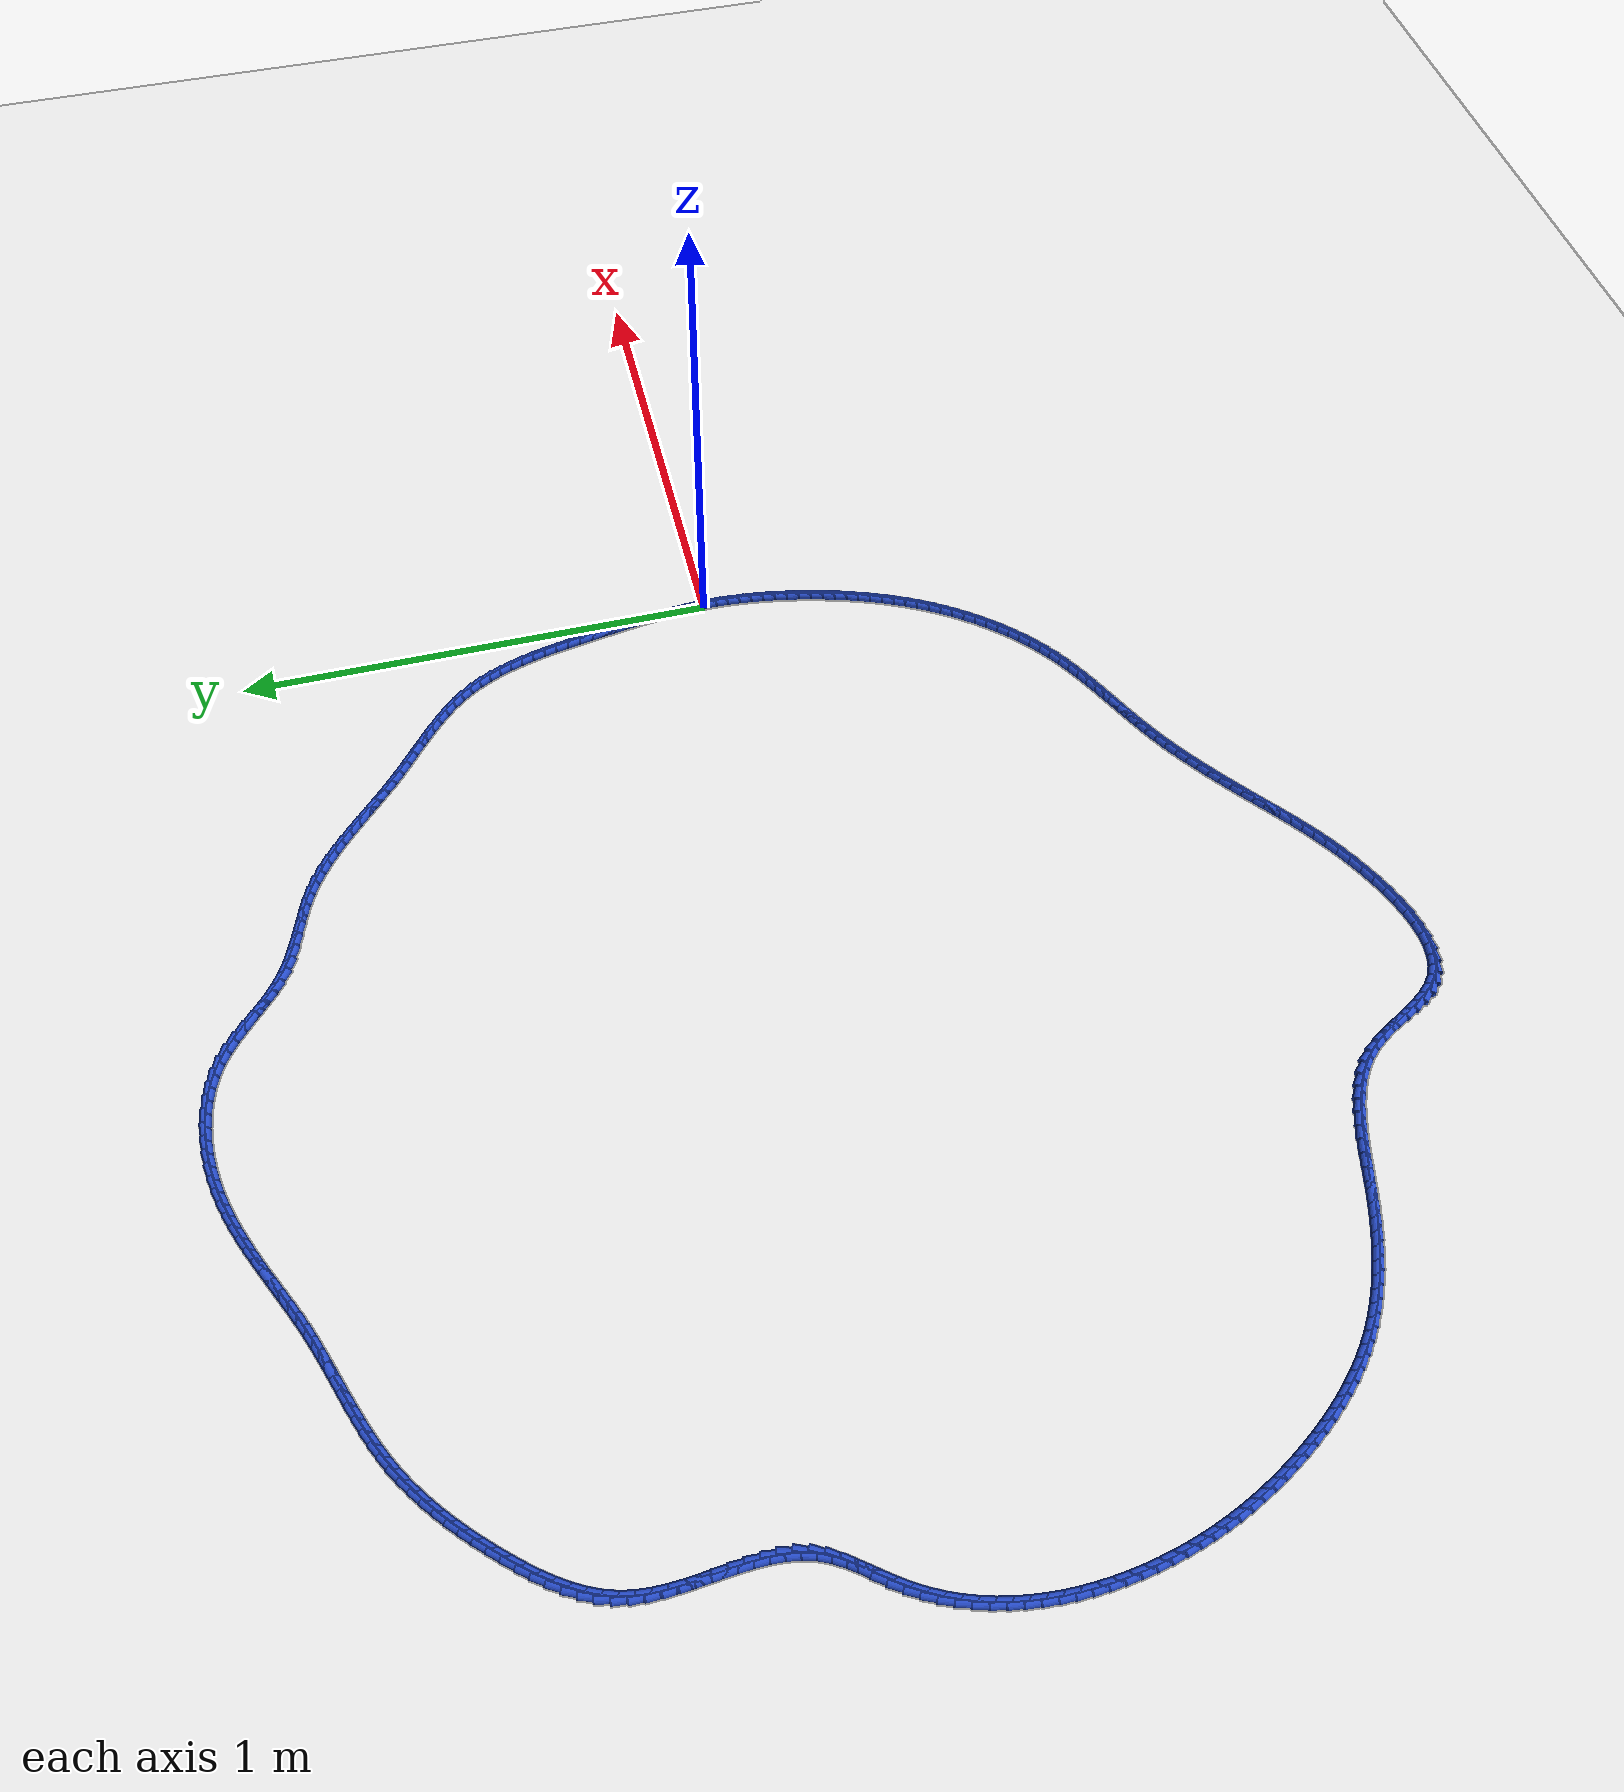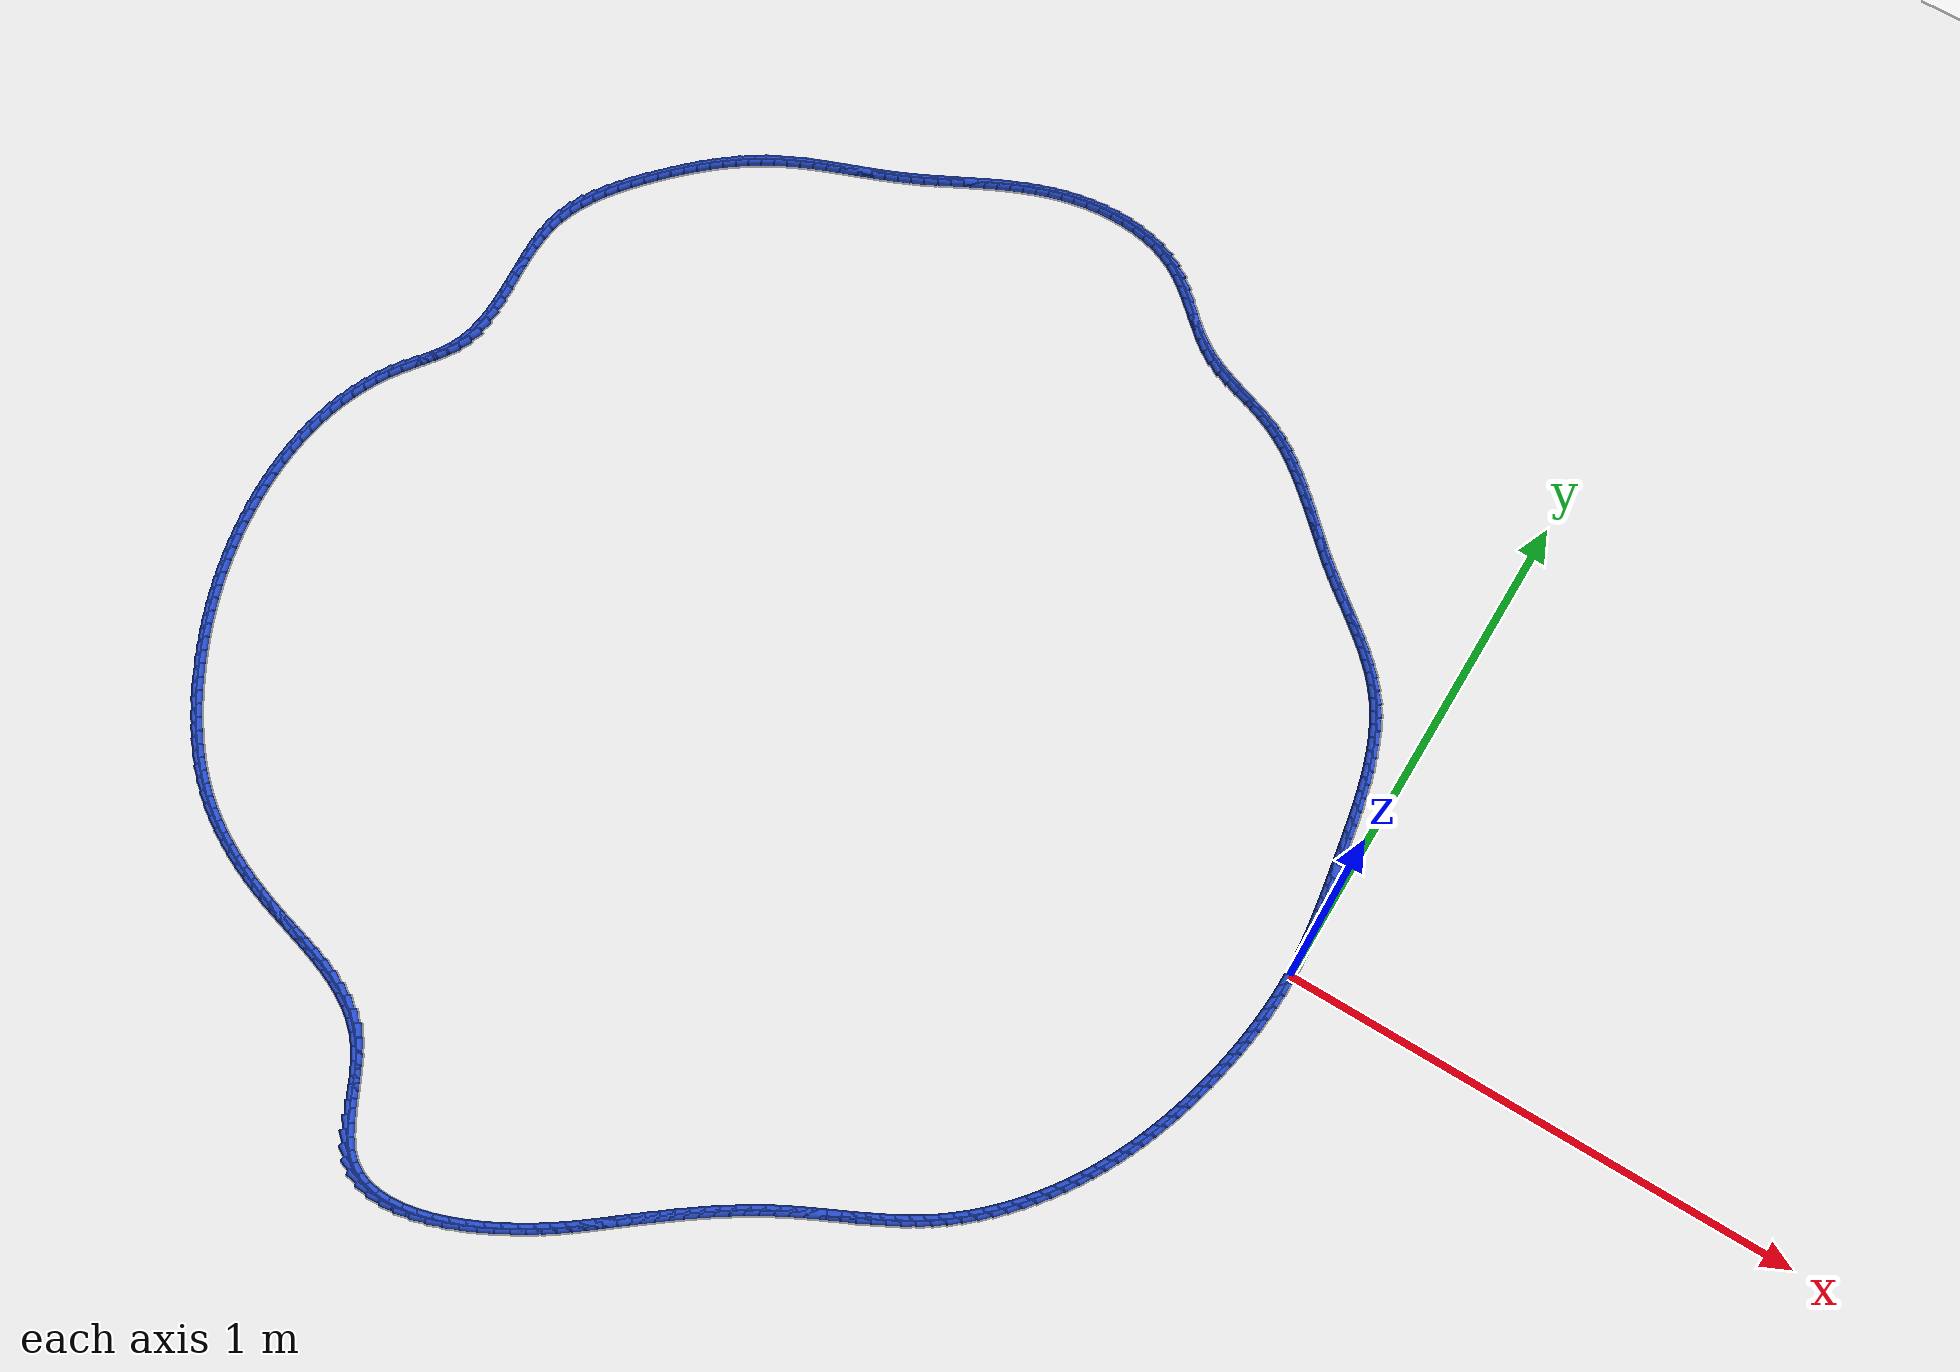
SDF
<sdf version="1.6">
 <world name="default">
  <light name="sun" type="directional">
   <pose>0 0 10 0 -0 0</pose>
   <diffuse>0.8 0.8 0.8 1</diffuse>
   <specular>0.2 0.2 0.2 1</specular>
   <attenuation>
    <range>1000</range>
    <constant>0.9</constant>
    <linear>0.01</linear>
    <quadratic>0.001</quadratic>
   </attenuation>
   <direction>-0.5 0.1 -0.9</direction>
  </light>
  <model name="ground_plane">
   <static>1</static>
   <link name="link">
    <collision name="collision">
     <geometry><plane><normal>0 0 1</normal><size>100 100</size></plane></geometry>
     <surface><friction><ode><mu>100</mu><mu2>50</mu2></ode></friction></surface>
    </collision>
    <visual name="visual">
     <cast_shadows>0</cast_shadows>
     <geometry><plane><normal>0 0 1</normal><size>100 100</size></plane></geometry>
     <material>
      <script><uri>file://media/materials/scripts/gazebo.material</uri><name>Gazebo/WhiteGlow</name></script>
     </material>
    </visual>
   </link>
  </model>
  <gravity>0 0 -9.8</gravity>
  <magnetic_field>6e-06 2.3e-05 -4.2e-05</magnetic_field>
  <atmosphere type="adiabatic"/>
  <physics name="default_physics" default="0" type="ode">
   <max_step_size>0.001</max_step_size>
   <real_time_factor>1</real_time_factor>
   <real_time_update_rate>1000</real_time_update_rate>
  </physics>
  <scene><ambient>0.4 0.4 0.4 1</ambient><background>0.7 0.7 0.7 1</background><shadows>1</shadows></scene>
  <spherical_coordinates>
   <surface_model>EARTH_WGS84</surface_model>
   <latitude_deg>0</latitude_deg>
   <longitude_deg>0</longitude_deg>
   <elevation>0</elevation>
   <heading_deg>0</heading_deg>
  </spherical_coordinates>
  <model name="line">
   <link name="link_0">
    <pose>4.336808689942018e-18 5.551115123125783e-17 0.01 0 1.57 -1.5379100877895757</pose>
    <collision name="collision">
     <geometry><cylinder><radius>0.01</radius><length>0.08</length></cylinder></geometry>
    </collision>
    <visual name="visual">
     <material>
      <script><name>Gazebo/Blue</name><uri>file://media/materials/scripts/gazebo.material</uri></script>
     </material>
     <geometry><cylinder><radius>0.01</radius><length>0.08</length></cylinder></geometry>
    </visual>
   </link>
   <link name="link_1">
    <pose>-0.0008520861090104348 0.0259007698734091 0.01 0 1.57 -1.5074474729927114</pose>
    <collision name="collision">
     <geometry><cylinder><radius>0.01</radius><length>0.08</length></cylinder></geometry>
    </collision>
    <visual name="visual">
     <material>
      <script><name>Gazebo/Blue</name><uri>file://media/materials/scripts/gazebo.material</uri></script>
     </material>
     <geometry><cylinder><radius>0.01</radius><length>0.08</length></cylinder></geometry>
    </visual>
   </link>
   <link name="link_2">
    <pose>-0.002491036457328171 0.05173797531334401 0.01 0 1.57 -1.480697998751893</pose>
    <collision name="collision">
     <geometry><cylinder><radius>0.01</radius><length>0.08</length></cylinder></geometry>
    </collision>
    <visual name="visual">
     <material>
      <script><name>Gazebo/Blue</name><uri>file://media/materials/scripts/gazebo.material</uri></script>
     </material>
     <geometry><cylinder><radius>0.01</radius><length>0.08</length></cylinder></geometry>
    </visual>
   </link>
   <link name="link_3">
    <pose>-0.004822410297093209 0.07754380326106165 0.01 0 1.57 -1.4577683714966108</pose>
    <collision name="collision">
     <geometry><cylinder><radius>0.01</radius><length>0.08</length></cylinder></geometry>
    </collision>
    <visual name="visual">
     <material>
      <script><name>Gazebo/Blue</name><uri>file://media/materials/scripts/gazebo.material</uri></script>
     </material>
     <geometry><cylinder><radius>0.01</radius><length>0.08</length></cylinder></geometry>
    </visual>
   </link>
   <link name="link_4">
    <pose>-0.007751766880445566 0.10335044065781888 0.01 0 1.57 -1.4387157896080138</pose>
    <collision name="collision">
     <geometry><cylinder><radius>0.01</radius><length>0.08</length></cylinder></geometry>
    </collision>
    <visual name="visual">
     <material>
      <script><name>Gazebo/Blue</name><uri>file://media/materials/scripts/gazebo.material</uri></script>
     </material>
     <geometry><cylinder><radius>0.01</radius><length>0.08</length></cylinder></geometry>
    </visual>
   </link>
   <link name="link_5">
    <pose>-0.011184665459525256 0.1291900744448726 0.01 0 1.57 -1.4235574689396657</pose>
    <collision name="collision">
     <geometry><cylinder><radius>0.01</radius><length>0.08</length></cylinder></geometry>
    </collision>
    <visual name="visual">
     <material>
      <script><name>Gazebo/Blue</name><uri>file://media/materials/scripts/gazebo.material</uri></script>
     </material>
     <geometry><cylinder><radius>0.01</radius><length>0.08</length></cylinder></geometry>
    </visual>
   </link>
   <link name="link_6">
    <pose>-0.015026665286472288 0.15509489156347964 0.01 0 1.57 -1.4122794236529297</pose>
    <collision name="collision">
     <geometry><cylinder><radius>0.01</radius><length>0.08</length></cylinder></geometry>
    </collision>
    <visual name="visual">
     <material>
      <script><name>Gazebo/Blue</name><uri>file://media/materials/scripts/gazebo.material</uri></script>
     </material>
     <geometry><cylinder><radius>0.01</radius><length>0.08</length></cylinder></geometry>
    </visual>
   </link>
   <link name="link_7">
    <pose>-0.019183325613426686 0.1810970789548969 0.01 0 1.57 -1.4048439143615312</pose>
    <collision name="collision">
     <geometry><cylinder><radius>0.01</radius><length>0.08</length></cylinder></geometry>
    </collision>
    <visual name="visual">
     <material>
      <script><name>Gazebo/Blue</name><uri>file://media/materials/scripts/gazebo.material</uri></script>
     </material>
     <geometry><cylinder><radius>0.01</radius><length>0.08</length></cylinder></geometry>
    </visual>
   </link>
   <link name="link_8">
    <pose>-0.02356020569252844 0.20722882356038114 0.01 0 1.57 -1.401195258315955</pose>
    <collision name="collision">
     <geometry><cylinder><radius>0.01</radius><length>0.08</length></cylinder></geometry>
    </collision>
    <visual name="visual">
     <material>
      <script><name>Gazebo/Blue</name><uri>file://media/materials/scripts/gazebo.material</uri></script>
     </material>
     <geometry><cylinder><radius>0.01</radius><length>0.08</length></cylinder></geometry>
    </visual>
   </link>
   <link name="link_9">
    <pose>-0.028062864775917587 0.23352231232118936 0.01 0 1.57 -1.4005227654413412</pose>
    <collision name="collision">
     <geometry><cylinder><radius>0.01</radius><length>0.08</length></cylinder></geometry>
    </collision>
    <visual name="visual">
     <material>
      <script><name>Gazebo/Blue</name><uri>file://media/materials/scripts/gazebo.material</uri></script>
     </material>
     <geometry><cylinder><radius>0.01</radius><length>0.08</length></cylinder></geometry>
    </visual>
   </link>
   <link name="link_10">
    <pose>-0.032615106125894626 0.25999830504153576 0.01 0 1.57 -1.3969650446520663</pose>
    <collision name="collision">
     <geometry><cylinder><radius>0.01</radius><length>0.08</length></cylinder></geometry>
    </collision>
    <visual name="visual">
     <material>
      <script><name>Gazebo/Blue</name><uri>file://media/materials/scripts/gazebo.material</uri></script>
     </material>
     <geometry><cylinder><radius>0.01</radius><length>0.08</length></cylinder></geometry>
    </visual>
   </link>
   <link name="link_11">
    <pose>-0.03728429017498857 0.28658764448200225 0.01 0 1.57 -1.3877890538961433</pose>
    <collision name="collision">
     <geometry><cylinder><radius>0.01</radius><length>0.08</length></cylinder></geometry>
    </collision>
    <visual name="visual">
     <material>
      <script><name>Gazebo/Blue</name><uri>file://media/materials/scripts/gazebo.material</uri></script>
     </material>
     <geometry><cylinder><radius>0.01</radius><length>0.08</length></cylinder></geometry>
    </visual>
   </link>
   <link name="link_12">
    <pose>-0.04220569914650027 0.3131786305847607 0.01 0 1.57 -1.3729220412109868</pose>
    <collision name="collision">
     <geometry><cylinder><radius>0.01</radius><length>0.08</length></cylinder></geometry>
    </collision>
    <visual name="visual">
     <material>
      <script><name>Gazebo/Blue</name><uri>file://media/materials/scripts/gazebo.material</uri></script>
     </material>
     <geometry><cylinder><radius>0.01</radius><length>0.08</length></cylinder></geometry>
    </visual>
   </link>
   <link name="link_13">
    <pose>-0.04751502027715108 0.3396593096117989 0.01 0 1.57 -1.35221025343579</pose>
    <collision name="collision">
     <geometry><cylinder><radius>0.01</radius><length>0.08</length></cylinder></geometry>
    </collision>
    <visual name="visual">
     <material>
      <script><name>Gazebo/Blue</name><uri>file://media/materials/scripts/gazebo.material</uri></script>
     </material>
     <geometry><cylinder><radius>0.01</radius><length>0.08</length></cylinder></geometry>
    </visual>
   </link>
   <link name="link_14">
    <pose>-0.053347940803662376 0.36591772782510434 0.01 0 1.57 -1.3254126780202675</pose>
    <collision name="collision">
     <geometry><cylinder><radius>0.01</radius><length>0.08</length></cylinder></geometry>
    </collision>
    <visual name="visual">
     <material>
      <script><name>Gazebo/Blue</name><uri>file://media/materials/scripts/gazebo.material</uri></script>
     </material>
     <geometry><cylinder><radius>0.01</radius><length>0.08</length></cylinder></geometry>
    </visual>
   </link>
   <link name="link_15">
    <pose>-0.05984014796275553 0.39184193148666485 0.01 0 1.57 -1.2922157415899456</pose>
    <collision name="collision">
     <geometry><cylinder><radius>0.01</radius><length>0.08</length></cylinder></geometry>
    </collision>
    <visual name="visual">
     <material>
      <script><name>Gazebo/Blue</name><uri>file://media/materials/scripts/gazebo.material</uri></script>
     </material>
     <geometry><cylinder><radius>0.01</radius><length>0.08</length></cylinder></geometry>
    </visual>
   </link>
   <link name="link_16">
    <pose>-0.06712732899115192 0.41731996685846817 0.01 0 1.57 -1.2522561096804858</pose>
    <collision name="collision">
     <geometry><cylinder><radius>0.01</radius><length>0.08</length></cylinder></geometry>
    </collision>
    <visual name="visual">
     <material>
      <script><name>Gazebo/Blue</name><uri>file://media/materials/scripts/gazebo.material</uri></script>
     </material>
     <geometry><cylinder><radius>0.01</radius><length>0.08</length></cylinder></geometry>
    </visual>
   </link>
   <link name="link_17">
    <pose>-0.07534517112557293 0.44223988020250193 0.01 0 1.57 -1.2051562475896969</pose>
    <collision name="collision">
     <geometry><cylinder><radius>0.01</radius><length>0.08</length></cylinder></geometry>
    </collision>
    <visual name="visual">
     <material>
      <script><name>Gazebo/Blue</name><uri>file://media/materials/scripts/gazebo.material</uri></script>
     </material>
     <geometry><cylinder><radius>0.01</radius><length>0.08</length></cylinder></geometry>
    </visual>
   </link>
   <link name="link_18">
    <pose>-0.0846293616027399 0.4664897177807539 0.01 0 1.57 -1.150577957239863</pose>
    <collision name="collision">
     <geometry><cylinder><radius>0.01</radius><length>0.08</length></cylinder></geometry>
    </collision>
    <visual name="visual">
     <material>
      <script><name>Gazebo/Blue</name><uri>file://media/materials/scripts/gazebo.material</uri></script>
     </material>
     <geometry><cylinder><radius>0.01</radius><length>0.08</length></cylinder></geometry>
    </visual>
   </link>
   <link name="link_19">
    <pose>-0.0951155876593742 0.4899575258552115 0.01 0 1.57 -1.0882981726788168</pose>
    <collision name="collision">
     <geometry><cylinder><radius>0.01</radius><length>0.08</length></cylinder></geometry>
    </collision>
    <visual name="visual">
     <material>
      <script><name>Gazebo/Blue</name><uri>file://media/materials/scripts/gazebo.material</uri></script>
     </material>
     <geometry><cylinder><radius>0.01</radius><length>0.08</length></cylinder></geometry>
    </visual>
   </link>
   <link name="link_20">
    <pose>-0.10693953653219725 0.5125313506878628 0.01 0 1.57 -1.0183073336183666</pose>
    <collision name="collision">
     <geometry><cylinder><radius>0.01</radius><length>0.08</length></cylinder></geometry>
    </collision>
    <visual name="visual">
     <material>
      <script><name>Gazebo/Blue</name><uri>file://media/materials/scripts/gazebo.material</uri></script>
     </material>
     <geometry><cylinder><radius>0.01</radius><length>0.08</length></cylinder></geometry>
    </visual>
   </link>
   <link name="link_21">
    <pose>-0.12023689545793037 0.5340992385406953 0.01 0 1.57 -0.9420895317729406</pose>
    <collision name="collision">
     <geometry><cylinder><radius>0.01</radius><length>0.08</length></cylinder></geometry>
    </collision>
    <visual name="visual">
     <material>
      <script><name>Gazebo/Blue</name><uri>file://media/materials/scripts/gazebo.material</uri></script>
     </material>
     <geometry><cylinder><radius>0.01</radius><length>0.08</length></cylinder></geometry>
    </visual>
   </link>
   <link name="link_22">
    <pose>-0.1351202324993757 0.554567677558318 0.01 0 1.57 -0.8710030178113921</pose>
    <collision name="collision">
     <geometry><cylinder><radius>0.01</radius><length>0.08</length></cylinder></geometry>
    </collision>
    <visual name="visual">
     <material>
      <script><name>Gazebo/Blue</name><uri>file://media/materials/scripts/gazebo.material</uri></script>
     </material>
     <geometry><cylinder><radius>0.01</radius><length>0.08</length></cylinder></geometry>
    </visual>
   </link>
   <link name="link_23">
    <pose>-0.15149083258360527 0.5740116938617681 0.01 0 1.57 -0.8113089329092253</pose>
    <collision name="collision">
     <geometry><cylinder><radius>0.01</radius><length>0.08</length></cylinder></geometry>
    </collision>
    <visual name="visual">
     <material>
      <script><name>Gazebo/Blue</name><uri>file://media/materials/scripts/gazebo.material</uri></script>
     </material>
     <geometry><cylinder><radius>0.01</radius><length>0.08</length></cylinder></geometry>
    </visual>
   </link>
   <link name="link_24">
    <pose>-0.1691367751752937 0.5925966161865669 0.01 0 1.57 -0.7630994874894123</pose>
    <collision name="collision">
     <geometry><cylinder><radius>0.01</radius><length>0.08</length></cylinder></geometry>
    </collision>
    <visual name="visual">
     <material>
      <script><name>Gazebo/Blue</name><uri>file://media/materials/scripts/gazebo.material</uri></script>
     </material>
     <geometry><cylinder><radius>0.01</radius><length>0.08</length></cylinder></geometry>
    </visual>
   </link>
   <link name="link_25">
    <pose>-0.18784506398596304 0.6104886313833853 0.01 0 1.57 -0.7260915848996364</pose>
    <collision name="collision">
     <geometry><cylinder><radius>0.01</radius><length>0.08</length></cylinder></geometry>
    </collision>
    <visual name="visual">
     <material>
      <script><name>Gazebo/Blue</name><uri>file://media/materials/scripts/gazebo.material</uri></script>
     </material>
     <geometry><cylinder><radius>0.01</radius><length>0.08</length></cylinder></geometry>
    </visual>
   </link>
   <link name="link_26">
    <pose>-0.20740270272713535 0.6278539263028938 0.01 0 1.57 -0.699872420583987</pose>
    <collision name="collision">
     <geometry><cylinder><radius>0.01</radius><length>0.08</length></cylinder></geometry>
    </collision>
    <visual name="visual">
     <material>
      <script><name>Gazebo/Blue</name><uri>file://media/materials/scripts/gazebo.material</uri></script>
     </material>
     <geometry><cylinder><radius>0.01</radius><length>0.08</length></cylinder></geometry>
    </visual>
   </link>
   <link name="link_27">
    <pose>-0.22759669511033276 0.6448586877957634 0.01 0 1.57 -0.6840325812757173</pose>
    <collision name="collision">
     <geometry><cylinder><radius>0.01</radius><length>0.08</length></cylinder></geometry>
    </collision>
    <visual name="visual">
     <material>
      <script><name>Gazebo/Blue</name><uri>file://media/materials/scripts/gazebo.material</uri></script>
     </material>
     <geometry><cylinder><radius>0.01</radius><length>0.08</length></cylinder></geometry>
    </visual>
   </link>
   <link name="link_28">
    <pose>-0.24821404484707732 0.6616691027126641 0.01 0 1.57 -0.6782467447179322</pose>
    <collision name="collision">
     <geometry><cylinder><radius>0.01</radius><length>0.08</length></cylinder></geometry>
    </collision>
    <visual name="visual">
     <material>
      <script><name>Gazebo/Blue</name><uri>file://media/materials/scripts/gazebo.material</uri></script>
     </material>
     <geometry><cylinder><radius>0.01</radius><length>0.08</length></cylinder></geometry>
    </visual>
   </link>
   <link name="link_29">
    <pose>-0.269041755648891 0.6784513579042669 0.01 0 1.57 -0.6823139056688585</pose>
    <collision name="collision">
     <geometry><cylinder><radius>0.01</radius><length>0.08</length></cylinder></geometry>
    </collision>
    <visual name="visual">
     <material>
      <script><name>Gazebo/Blue</name><uri>file://media/materials/scripts/gazebo.material</uri></script>
     </material>
     <geometry><cylinder><radius>0.01</radius><length>0.08</length></cylinder></geometry>
    </visual>
   </link>
   <link name="link_30">
    <pose>-0.28986683122729595 0.6953716402212424 0.01 0 1.57 -0.696167194310899</pose>
    <collision name="collision">
     <geometry><cylinder><radius>0.01</radius><length>0.08</length></cylinder></geometry>
    </collision>
    <visual name="visual">
     <material>
      <script><name>Gazebo/Blue</name><uri>file://media/materials/scripts/gazebo.material</uri></script>
     </material>
     <geometry><cylinder><radius>0.01</radius><length>0.08</length></cylinder></geometry>
    </visual>
   </link>
   <link name="link_31">
    <pose>-0.3104762752938142 0.7125961365142612 0.01 0 1.57 -0.7189831504060218</pose>
    <collision name="collision">
     <geometry><cylinder><radius>0.01</radius><length>0.08</length></cylinder></geometry>
    </collision>
    <visual name="visual">
     <material>
      <script><name>Gazebo/Blue</name><uri>file://media/materials/scripts/gazebo.material</uri></script>
     </material>
     <geometry><cylinder><radius>0.01</radius><length>0.08</length></cylinder></geometry>
    </visual>
   </link>
   <link name="link_32">
    <pose>-0.33067357273106607 0.7302742339915279 0.01 0 1.57 -0.7404757256802703</pose>
    <collision name="collision">
     <geometry><cylinder><radius>0.01</radius><length>0.08</length></cylinder></geometry>
    </collision>
    <visual name="visual">
     <material>
      <script><name>Gazebo/Blue</name><uri>file://media/materials/scripts/gazebo.material</uri></script>
     </material>
     <geometry><cylinder><radius>0.01</radius><length>0.08</length></cylinder></geometry>
    </visual>
   </link>
   <link name="link_33">
    <pose>-0.3504576332478125 0.7483561187736164 0.01 0 1.57 -0.7538716692492</pose>
    <collision name="collision">
     <geometry><cylinder><radius>0.01</radius><length>0.08</length></cylinder></geometry>
    </collision>
    <visual name="visual">
     <material>
      <script><name>Gazebo/Blue</name><uri>file://media/materials/scripts/gazebo.material</uri></script>
     </material>
     <geometry><cylinder><radius>0.01</radius><length>0.08</length></cylinder></geometry>
    </visual>
   </link>
   <link name="link_34">
    <pose>-0.36995529046351955 0.7666615811524354 0.01 0 1.57 -0.7590361274240356</pose>
    <collision name="collision">
     <geometry><cylinder><radius>0.01</radius><length>0.08</length></cylinder></geometry>
    </collision>
    <visual name="visual">
     <material>
      <script><name>Gazebo/Blue</name><uri>file://media/materials/scripts/gazebo.material</uri></script>
     </material>
     <geometry><cylinder><radius>0.01</radius><length>0.08</length></cylinder></geometry>
    </visual>
   </link>
   <link name="link_35">
    <pose>-0.38929559443232964 0.7850081521562844 0.01 0 1.57 -0.7559058540276596</pose>
    <collision name="collision">
     <geometry><cylinder><radius>0.01</radius><length>0.08</length></cylinder></geometry>
    </collision>
    <visual name="visual">
     <material>
      <script><name>Gazebo/Blue</name><uri>file://media/materials/scripts/gazebo.material</uri></script>
     </material>
     <geometry><cylinder><radius>0.01</radius><length>0.08</length></cylinder></geometry>
    </visual>
   </link>
   <link name="link_36">
    <pose>-0.4086075952083847 0.8032133628134619 0.01 0 1.57 -0.7443593580019027</pose>
    <collision name="collision">
     <geometry><cylinder><radius>0.01</radius><length>0.08</length></cylinder></geometry>
    </collision>
    <visual name="visual">
     <material>
      <script><name>Gazebo/Blue</name><uri>file://media/materials/scripts/gazebo.material</uri></script>
     </material>
     <geometry><cylinder><radius>0.01</radius><length>0.08</length></cylinder></geometry>
    </visual>
   </link>
   <link name="link_37">
    <pose>-0.4280203428458269 0.8210947441522676 0.01 0 1.57 -0.72422103832527</pose>
    <collision name="collision">
     <geometry><cylinder><radius>0.01</radius><length>0.08</length></cylinder></geometry>
    </collision>
    <visual name="visual">
     <material>
      <script><name>Gazebo/Blue</name><uri>file://media/materials/scripts/gazebo.material</uri></script>
     </material>
     <geometry><cylinder><radius>0.01</radius><length>0.08</length></cylinder></geometry>
    </visual>
   </link>
   <link name="link_38">
    <pose>-0.4476628873987986 0.8384698272010004 0.01 0 1.57 -0.6952835826102192</pose>
    <collision name="collision">
     <geometry><cylinder><radius>0.01</radius><length>0.08</length></cylinder></geometry>
    </collision>
    <visual name="visual">
     <material>
      <script><name>Gazebo/Blue</name><uri>file://media/materials/scripts/gazebo.material</uri></script>
     </material>
     <geometry><cylinder><radius>0.01</radius><length>0.08</length></cylinder></geometry>
    </visual>
   </link>
   <link name="link_39">
    <pose>-0.4676642789214419 0.8551561429879595 0.01 0 1.57 -0.6573519959993188</pose>
    <collision name="collision">
     <geometry><cylinder><radius>0.01</radius><length>0.08</length></cylinder></geometry>
    </collision>
    <visual name="visual">
     <material>
      <script><name>Gazebo/Blue</name><uri>file://media/materials/scripts/gazebo.material</uri></script>
     </material>
     <geometry><cylinder><radius>0.01</radius><length>0.08</length></cylinder></geometry>
    </visual>
   </link>
   <link name="link_40">
    <pose>-0.48815356746789873 0.8709712225414437 0.01 0 1.57 -0.6103127672021218</pose>
    <collision name="collision">
     <geometry><cylinder><radius>0.01</radius><length>0.08</length></cylinder></geometry>
    </collision>
    <visual name="visual">
     <material>
      <script><name>Gazebo/Blue</name><uri>file://media/materials/scripts/gazebo.material</uri></script>
     </material>
     <geometry><cylinder><radius>0.01</radius><length>0.08</length></cylinder></geometry>
    </visual>
   </link>
   <link name="link_41">
    <pose>-0.5092598030923114 0.8857325968897525 0.01 0 1.57 -0.5542290019331925</pose>
    <collision name="collision">
     <geometry><cylinder><radius>0.01</radius><length>0.08</length></cylinder></geometry>
    </collision>
    <visual name="visual">
     <material>
      <script><name>Gazebo/Blue</name><uri>file://media/materials/scripts/gazebo.material</uri></script>
     </material>
     <geometry><cylinder><radius>0.01</radius><length>0.08</length></cylinder></geometry>
    </visual>
   </link>
   <link name="link_42">
    <pose>-0.5311120358488224 0.8992577970611848 0.01 0 1.57 -0.4894550342461614</pose>
    <collision name="collision">
     <geometry><cylinder><radius>0.01</radius><length>0.08</length></cylinder></geometry>
    </collision>
    <visual name="visual">
     <material>
      <script><name>Gazebo/Blue</name><uri>file://media/materials/scripts/gazebo.material</uri></script>
     </material>
     <geometry><cylinder><radius>0.01</radius><length>0.08</length></cylinder></geometry>
    </visual>
   </link>
   <link name="link_43">
    <pose>-0.5538393157915735 0.91136435408404 0.01 0 1.57 -0.41960881596879585</pose>
    <collision name="collision">
     <geometry><cylinder><radius>0.01</radius><length>0.08</length></cylinder></geometry>
    </collision>
    <visual name="visual">
     <material>
      <script><name>Gazebo/Blue</name><uri>file://media/materials/scripts/gazebo.material</uri></script>
     </material>
     <geometry><cylinder><radius>0.01</radius><length>0.08</length></cylinder></geometry>
    </visual>
   </link>
   <link name="link_44">
    <pose>-0.5775306258490446 0.9219331287975742 0.01 0 1.57 -0.36639053939485766</pose>
    <collision name="collision">
     <geometry><cylinder><radius>0.01</radius><length>0.08</length></cylinder></geometry>
    </collision>
    <visual name="visual">
     <material>
      <script><name>Gazebo/Blue</name><uri>file://media/materials/scripts/gazebo.material</uri></script>
     </material>
     <geometry><cylinder><radius>0.01</radius><length>0.08</length></cylinder></geometry>
    </visual>
   </link>
   <link name="link_45">
    <pose>-0.6019781771864022 0.931314057357964 0.01 0 1.57 -0.3385262993515373</pose>
    <collision name="collision">
     <geometry><cylinder><radius>0.01</radius><length>0.08</length></cylinder></geometry>
    </collision>
    <visual name="visual">
     <material>
      <script><name>Gazebo/Blue</name><uri>file://media/materials/scripts/gazebo.material</uri></script>
     </material>
     <geometry><cylinder><radius>0.01</radius><length>0.08</length></cylinder></geometry>
    </visual>
   </link>
   <link name="link_46">
    <pose>-0.6268409119523912 0.940067719971263 0.01 0 1.57 -0.33525579726821875</pose>
    <collision name="collision">
     <geometry><cylinder><radius>0.01</radius><length>0.08</length></cylinder></geometry>
    </collision>
    <visual name="visual">
     <material>
      <script><name>Gazebo/Blue</name><uri>file://media/materials/scripts/gazebo.material</uri></script>
     </material>
     <geometry><cylinder><radius>0.01</radius><length>0.08</length></cylinder></geometry>
    </visual>
   </link>
   <link name="link_47">
    <pose>-0.6517771381834858 0.9487556991168247 0.01 0 1.57 -0.35640045772413664</pose>
    <collision name="collision">
     <geometry><cylinder><radius>0.01</radius><length>0.08</length></cylinder></geometry>
    </collision>
    <visual name="visual">
     <material>
      <script><name>Gazebo/Blue</name><uri>file://media/materials/scripts/gazebo.material</uri></script>
     </material>
     <geometry><cylinder><radius>0.01</radius><length>0.08</length></cylinder></geometry>
    </visual>
   </link>
   <link name="link_48">
    <pose>-0.6764451639161606 0.9579395772740014 0.01 0 1.57 -0.40245679982876137</pose>
    <collision name="collision">
     <geometry><cylinder><radius>0.01</radius><length>0.08</length></cylinder></geometry>
    </collision>
    <visual name="visual">
     <material>
      <script><name>Gazebo/Blue</name><uri>file://media/materials/scripts/gazebo.material</uri></script>
     </material>
     <geometry><cylinder><radius>0.01</radius><length>0.08</length></cylinder></geometry>
    </visual>
   </link>
   <link name="link_49">
    <pose>-0.7005032971868895 0.9681809369221455 0.01 0 1.57 -0.4742251573824438</pose>
    <collision name="collision">
     <geometry><cylinder><radius>0.01</radius><length>0.08</length></cylinder></geometry>
    </collision>
    <visual name="visual">
     <material>
      <script><name>Gazebo/Blue</name><uri>file://media/materials/scripts/gazebo.material</uri></script>
     </material>
     <geometry><cylinder><radius>0.01</radius><length>0.08</length></cylinder></geometry>
    </visual>
   </link>
   <link name="link_50">
    <pose>-0.7236098460321476 0.98004136054061 0.01 0 1.57 -0.5691463390385256</pose>
    <collision name="collision">
     <geometry><cylinder><radius>0.01</radius><length>0.08</length></cylinder></geometry>
    </collision>
    <visual name="visual">
     <material>
      <script><name>Gazebo/Blue</name><uri>file://media/materials/scripts/gazebo.material</uri></script>
     </material>
     <geometry><cylinder><radius>0.01</radius><length>0.08</length></cylinder></geometry>
    </visual>
   </link>
   <link name="link_51">
    <pose>-0.7454601948358864 0.9940204452381693 0.01 0 1.57 -0.6547121877764799</pose>
    <collision name="collision">
     <geometry><cylinder><radius>0.01</radius><length>0.08</length></cylinder></geometry>
    </collision>
    <visual name="visual">
     <material>
      <script><name>Gazebo/Blue</name><uri>file://media/materials/scripts/gazebo.material</uri></script>
     </material>
     <geometry><cylinder><radius>0.01</radius><length>0.08</length></cylinder></geometry>
    </visual>
   </link>
   <link name="link_52">
    <pose>-0.7661685626642528 1.0099175675044452 0.01 0 1.57 -0.7108308987216927</pose>
    <collision name="collision">
     <geometry><cylinder><radius>0.01</radius><length>0.08</length></cylinder></geometry>
    </collision>
    <visual name="visual">
     <material>
      <script><name>Gazebo/Blue</name><uri>file://media/materials/scripts/gazebo.material</uri></script>
     </material>
     <geometry><cylinder><radius>0.01</radius><length>0.08</length></cylinder></geometry>
    </visual>
   </link>
   <link name="link_53">
    <pose>-0.786113712180207 1.0270898317608 0.01 0 1.57 -0.7381318162916466</pose>
    <collision name="collision">
     <geometry><cylinder><radius>0.01</radius><length>0.08</length></cylinder></geometry>
    </collision>
    <visual name="visual">
     <material>
      <script><name>Gazebo/Blue</name><uri>file://media/materials/scripts/gazebo.material</uri></script>
     </material>
     <geometry><cylinder><radius>0.01</radius><length>0.08</length></cylinder></geometry>
    </visual>
   </link>
   <link name="link_54">
    <pose>-0.8056785671275642 1.0448873858064789 0.01 0 1.57 -0.7373775400622639</pose>
    <collision name="collision">
     <geometry><cylinder><radius>0.01</radius><length>0.08</length></cylinder></geometry>
    </collision>
    <visual name="visual">
     <material>
      <script><name>Gazebo/Blue</name><uri>file://media/materials/scripts/gazebo.material</uri></script>
     </material>
     <geometry><cylinder><radius>0.01</radius><length>0.08</length></cylinder></geometry>
    </visual>
   </link>
   <link name="link_55">
    <pose>-0.8252460512501404 1.0626603774407275 0.01 0 1.57 -0.7085099393509378</pose>
    <collision name="collision">
     <geometry><cylinder><radius>0.01</radius><length>0.08</length></cylinder></geometry>
    </collision>
    <visual name="visual">
     <material>
      <script><name>Gazebo/Blue</name><uri>file://media/materials/scripts/gazebo.material</uri></script>
     </material>
     <geometry><cylinder><radius>0.01</radius><length>0.08</length></cylinder></geometry>
    </visual>
   </link>
   <link name="link_56">
    <pose>-0.8451990882917504 1.079758954462792 0.01 0 1.57 -0.6506640842835053</pose>
    <collision name="collision">
     <geometry><cylinder><radius>0.01</radius><length>0.08</length></cylinder></geometry>
    </collision>
    <visual name="visual">
     <material>
      <script><name>Gazebo/Blue</name><uri>file://media/materials/scripts/gazebo.material</uri></script>
     </material>
     <geometry><cylinder><radius>0.01</radius><length>0.08</length></cylinder></geometry>
    </visual>
   </link>
   <link name="link_57">
    <pose>-0.8659206019962098 1.0955332646719178 0.01 0 1.57 -0.5628547343251302</pose>
    <collision name="collision">
     <geometry><cylinder><radius>0.01</radius><length>0.08</length></cylinder></geometry>
    </collision>
    <visual name="visual">
     <material>
      <script><name>Gazebo/Blue</name><uri>file://media/materials/scripts/gazebo.material</uri></script>
     </material>
     <geometry><cylinder><radius>0.01</radius><length>0.08</length></cylinder></geometry>
    </visual>
   </link>
   <link name="link_58">
    <pose>-0.8877934293471321 1.1093335643801594 0.01 0 1.57 -0.45359936086249925</pose>
    <collision name="collision">
     <geometry><cylinder><radius>0.01</radius><length>0.08</length></cylinder></geometry>
    </collision>
    <visual name="visual">
     <material>
      <script><name>Gazebo/Blue</name><uri>file://media/materials/scripts/gazebo.material</uri></script>
     </material>
     <geometry><cylinder><radius>0.01</radius><length>0.08</length></cylinder></geometry>
    </visual>
   </link>
   <link name="link_59">
    <pose>-0.9110655543980816 1.1206787732922852 0.01 0 1.57 -0.3489515506930772</pose>
    <collision name="collision">
     <geometry><cylinder><radius>0.01</radius><length>0.08</length></cylinder></geometry>
    </collision>
    <visual name="visual">
     <material>
      <script><name>Gazebo/Blue</name><uri>file://media/materials/scripts/gazebo.material</uri></script>
     </material>
     <geometry><cylinder><radius>0.01</radius><length>0.08</length></cylinder></geometry>
    </visual>
   </link>
   <link name="link_60">
    <pose>-0.935577631462763 1.1295972669762422 0.01 0 1.57 -0.25369937874503556</pose>
    <collision name="collision">
     <geometry><cylinder><radius>0.01</radius><length>0.08</length></cylinder></geometry>
    </collision>
    <visual name="visual">
     <material>
      <script><name>Gazebo/Blue</name><uri>file://media/materials/scripts/gazebo.material</uri></script>
     </material>
     <geometry><cylinder><radius>0.01</radius><length>0.08</length></cylinder></geometry>
    </visual>
   </link>
   <link name="link_61">
    <pose>-0.9610937081624976 1.1362132345995544 0.01 0 1.57 -0.16725583737513247</pose>
    <collision name="collision">
     <geometry><cylinder><radius>0.01</radius><length>0.08</length></cylinder></geometry>
    </collision>
    <visual name="visual">
     <material>
      <script><name>Gazebo/Blue</name><uri>file://media/materials/scripts/gazebo.material</uri></script>
     </material>
     <geometry><cylinder><radius>0.01</radius><length>0.08</length></cylinder></geometry>
    </visual>
   </link>
   <link name="link_62">
    <pose>-0.9873778321186074 1.1406508653297476 0.01 0 1.57 -0.0886491891348493</pose>
    <collision name="collision">
     <geometry><cylinder><radius>0.01</radius><length>0.08</length></cylinder></geometry>
    </collision>
    <visual name="visual">
     <material>
      <script><name>Gazebo/Blue</name><uri>file://media/materials/scripts/gazebo.material</uri></script>
     </material>
     <geometry><cylinder><radius>0.01</radius><length>0.08</length></cylinder></geometry>
    </visual>
   </link>
   <link name="link_63">
    <pose>-1.0141940509524145 1.1430343483343475 0.01 0 1.57 -0.016726029411488975</pose>
    <collision name="collision">
     <geometry><cylinder><radius>0.01</radius><length>0.08</length></cylinder></geometry>
    </collision>
    <visual name="visual">
     <material>
      <script><name>Gazebo/Blue</name><uri>file://media/materials/scripts/gazebo.material</uri></script>
     </material>
     <geometry><cylinder><radius>0.01</radius><length>0.08</length></cylinder></geometry>
    </visual>
   </link>
   <link name="link_64">
    <pose>-1.041306412285241 1.1434878727808795 0.01 0 1.57 0.049724086244175666</pose>
    <collision name="collision">
     <geometry><cylinder><radius>0.01</radius><length>0.08</length></cylinder></geometry>
    </collision>
    <visual name="visual">
     <material>
      <script><name>Gazebo/Blue</name><uri>file://media/materials/scripts/gazebo.material</uri></script>
     </material>
     <geometry><cylinder><radius>0.01</radius><length>0.08</length></cylinder></geometry>
    </visual>
   </link>
   <link name="link_65">
    <pose>-1.0684789637384084 1.1421356278368688 0.01 0 1.57 0.11190775363540284</pose>
    <collision name="collision">
     <geometry><cylinder><radius>0.01</radius><length>0.08</length></cylinder></geometry>
    </collision>
    <visual name="visual">
     <material>
      <script><name>Gazebo/Blue</name><uri>file://media/materials/scripts/gazebo.material</uri></script>
     </material>
     <geometry><cylinder><radius>0.01</radius><length>0.08</length></cylinder></geometry>
    </visual>
   </link>
   <link name="link_66">
    <pose>-1.0954757529332397 1.139101802669841 0.01 0 1.57 0.1710121874426664</pose>
    <collision name="collision">
     <geometry><cylinder><radius>0.01</radius><length>0.08</length></cylinder></geometry>
    </collision>
    <visual name="visual">
     <material>
      <script><name>Gazebo/Blue</name><uri>file://media/materials/scripts/gazebo.material</uri></script>
     </material>
     <geometry><cylinder><radius>0.01</radius><length>0.08</length></cylinder></geometry>
    </visual>
   </link>
   <link name="link_67">
    <pose>-1.1220608274910564 1.1345105864473222 0.01 0 1.57 0.22773385216797168</pose>
    <collision name="collision">
     <geometry><cylinder><radius>0.01</radius><length>0.08</length></cylinder></geometry>
    </collision>
    <visual name="visual">
     <material>
      <script><name>Gazebo/Blue</name><uri>file://media/materials/scripts/gazebo.material</uri></script>
     </material>
     <geometry><cylinder><radius>0.01</radius><length>0.08</length></cylinder></geometry>
    </visual>
   </link>
   <link name="link_68">
    <pose>-1.1480378824588584 1.1284902937943988 0.01 0 1.57 0.2800721633641779</pose>
    <collision name="collision">
     <geometry><cylinder><radius>0.01</radius><length>0.08</length></cylinder></geometry>
    </collision>
    <visual name="visual">
     <material>
      <script><name>Gazebo/Blue</name><uri>file://media/materials/scripts/gazebo.material</uri></script>
     </material>
     <geometry><cylinder><radius>0.01</radius><length>0.08</length></cylinder></geometry>
    </visual>
   </link>
   <link name="link_69">
    <pose>-1.17341628815771 1.1211906405898404 0.01 0 1.57 0.3267092540994791</pose>
    <collision name="collision">
     <geometry><cylinder><radius>0.01</radius><length>0.08</length></cylinder></geometry>
    </collision>
    <visual name="visual">
     <material>
      <script><name>Gazebo/Blue</name><uri>file://media/materials/scripts/gazebo.material</uri></script>
     </material>
     <geometry><cylinder><radius>0.01</radius><length>0.08</length></cylinder></geometry>
    </visual>
   </link>
   <link name="link_70">
    <pose>-1.1982719043565853 1.1127682611791503 0.01 0 1.57 0.3671916291564925</pose>
    <collision name="collision">
     <geometry><cylinder><radius>0.01</radius><length>0.08</length></cylinder></geometry>
    </collision>
    <visual name="visual">
     <material>
      <script><name>Gazebo/Blue</name><uri>file://media/materials/scripts/gazebo.material</uri></script>
     </material>
     <geometry><cylinder><radius>0.01</radius><length>0.08</length></cylinder></geometry>
    </visual>
   </link>
   <link name="link_71">
    <pose>-1.2226806242172712 1.103379793382475 0.01 0 1.57 0.40123229508254626</pose>
    <collision name="collision">
     <geometry><cylinder><radius>0.01</radius><length>0.08</length></cylinder></geometry>
    </collision>
    <visual name="visual">
     <material>
      <script><name>Gazebo/Blue</name><uri>file://media/materials/scripts/gazebo.material</uri></script>
     </material>
     <geometry><cylinder><radius>0.01</radius><length>0.08</length></cylinder></geometry>
    </visual>
   </link>
   <link name="link_72">
    <pose>-1.2467183409015585 1.093181875019961 0.01 0 1.57 0.4286723957342897</pose>
    <collision name="collision">
     <geometry><cylinder><radius>0.01</radius><length>0.08</length></cylinder></geometry>
    </collision>
    <visual name="visual">
     <material>
      <script><name>Gazebo/Blue</name><uri>file://media/materials/scripts/gazebo.material</uri></script>
     </material>
     <geometry><cylinder><radius>0.01</radius><length>0.08</length></cylinder></geometry>
    </visual>
   </link>
   <link name="link_73">
    <pose>-1.2704609475712354 1.082331143911755 0.01 0 1.57 0.4494419301533974</pose>
    <collision name="collision">
     <geometry><cylinder><radius>0.01</radius><length>0.08</length></cylinder></geometry>
    </collision>
    <visual name="visual">
     <material>
      <script><name>Gazebo/Blue</name><uri>file://media/materials/scripts/gazebo.material</uri></script>
     </material>
     <geometry><cylinder><radius>0.01</radius><length>0.08</length></cylinder></geometry>
    </visual>
   </link>
   <link name="link_74">
    <pose>-1.293984337388091 1.070984237878003 0.01 0 1.57 0.46352476437839174</pose>
    <collision name="collision">
     <geometry><cylinder><radius>0.01</radius><length>0.08</length></cylinder></geometry>
    </collision>
    <visual name="visual">
     <material>
      <script><name>Gazebo/Blue</name><uri>file://media/materials/scripts/gazebo.material</uri></script>
     </material>
     <geometry><cylinder><radius>0.01</radius><length>0.08</length></cylinder></geometry>
    </visual>
   </link>
   <link name="link_75">
    <pose>-1.317364403513915 1.0592977947388518 0.01 0 1.57 0.4709310440404485</pose>
    <collision name="collision">
     <geometry><cylinder><radius>0.01</radius><length>0.08</length></cylinder></geometry>
    </collision>
    <visual name="visual">
     <material>
      <script><name>Gazebo/Blue</name><uri>file://media/materials/scripts/gazebo.material</uri></script>
     </material>
     <geometry><cylinder><radius>0.01</radius><length>0.08</length></cylinder></geometry>
    </visual>
   </link>
   <link name="link_76">
    <pose>-1.3406770391104952 1.0474284523144484 0.01 0 1.57 0.4716783078131573</pose>
    <collision name="collision">
     <geometry><cylinder><radius>0.01</radius><length>0.08</length></cylinder></geometry>
    </collision>
    <visual name="visual">
     <material>
      <script><name>Gazebo/Blue</name><uri>file://media/materials/scripts/gazebo.material</uri></script>
     </material>
     <geometry><cylinder><radius>0.01</radius><length>0.08</length></cylinder></geometry>
    </visual>
   </link>
   <link name="link_77">
    <pose>-1.3639981373396206 1.0355328484249382 0.01 0 1.57 0.46578159845726524</pose>
    <collision name="collision">
     <geometry><cylinder><radius>0.01</radius><length>0.08</length></cylinder></geometry>
    </collision>
    <visual name="visual">
     <material>
      <script><name>Gazebo/Blue</name><uri>file://media/materials/scripts/gazebo.material</uri></script>
     </material>
     <geometry><cylinder><radius>0.01</radius><length>0.08</length></cylinder></geometry>
    </visual>
   </link>
   <link name="link_78">
    <pose>-1.3874035913630813 1.0237676208904685 0.01 0 1.57 0.4532524840691968</pose>
    <collision name="collision">
     <geometry><cylinder><radius>0.01</radius><length>0.08</length></cylinder></geometry>
    </collision>
    <visual name="visual">
     <material>
      <script><name>Gazebo/Blue</name><uri>file://media/materials/scripts/gazebo.material</uri></script>
     </material>
     <geometry><cylinder><radius>0.01</radius><length>0.08</length></cylinder></geometry>
    </visual>
   </link>
   <link name="link_79">
    <pose>-1.4109692943426655 1.0122894075311857 0.01 0 1.57 0.43410685240384517</pose>
    <collision name="collision">
     <geometry><cylinder><radius>0.01</radius><length>0.08</length></cylinder></geometry>
    </collision>
    <visual name="visual">
     <material>
      <script><name>Gazebo/Blue</name><uri>file://media/materials/scripts/gazebo.material</uri></script>
     </material>
     <geometry><cylinder><radius>0.01</radius><length>0.08</length></cylinder></geometry>
    </visual>
   </link>
   <link name="link_80">
    <pose>-1.4347711394401617 1.001254846167236 0.01 0 1.57 0.4094853175289217</pose>
    <collision name="collision">
     <geometry><cylinder><radius>0.01</radius><length>0.08</length></cylinder></geometry>
    </collision>
    <visual name="visual">
     <material>
      <script><name>Gazebo/Blue</name><uri>file://media/materials/scripts/gazebo.material</uri></script>
     </material>
     <geometry><cylinder><radius>0.01</radius><length>0.08</length></cylinder></geometry>
    </visual>
   </link>
   <link name="link_81">
    <pose>-1.4588714181545772 0.9907948568595815 0.01 0 1.57 0.3881277248245793</pose>
    <collision name="collision">
     <geometry><cylinder><radius>0.01</radius><length>0.08</length></cylinder></geometry>
    </collision>
    <visual name="visual">
     <material>
      <script><name>Gazebo/Blue</name><uri>file://media/materials/scripts/gazebo.material</uri></script>
     </material>
     <geometry><cylinder><radius>0.01</radius><length>0.08</length></cylinder></geometry>
    </visual>
   </link>
   <link name="link_82">
    <pose>-1.4832250908971338 0.9808374201379821 0.01 0 1.57 0.37411390209983686</pose>
    <collision name="collision">
     <geometry><cylinder><radius>0.01</radius><length>0.08</length></cylinder></geometry>
    </collision>
    <visual name="visual">
     <material>
      <script><name>Gazebo/Blue</name><uri>file://media/materials/scripts/gazebo.material</uri></script>
     </material>
     <geometry><cylinder><radius>0.01</radius><length>0.08</length></cylinder></geometry>
    </visual>
   </link>
   <link name="link_83">
    <pose>-1.5077362132667067 0.9712142667040542 0.01 0 1.57 0.3674158204303403</pose>
    <collision name="collision">
     <geometry><cylinder><radius>0.01</radius><length>0.08</length></cylinder></geometry>
    </collision>
    <visual name="visual">
     <material>
      <script><name>Gazebo/Blue</name><uri>file://media/materials/scripts/gazebo.material</uri></script>
     </material>
     <geometry><cylinder><radius>0.01</radius><length>0.08</length></cylinder></geometry>
    </visual>
   </link>
   <link name="link_84">
    <pose>-1.5323085342831964 0.961756547585861 0.01 0 1.57 0.368015777200567</pose>
    <collision name="collision">
     <geometry><cylinder><radius>0.01</radius><length>0.08</length></cylinder></geometry>
    </collision>
    <visual name="visual">
     <material>
      <script><name>Gazebo/Blue</name><uri>file://media/materials/scripts/gazebo.material</uri></script>
     </material>
     <geometry><cylinder><radius>0.01</radius><length>0.08</length></cylinder></geometry>
    </visual>
   </link>
   <link name="link_85">
    <pose>-1.5568458029665053 0.9522954138114669 0.01 0 1.57 0.3759419420897162</pose>
    <collision name="collision">
     <geometry><cylinder><radius>0.01</radius><length>0.08</length></cylinder></geometry>
    </collision>
    <visual name="visual">
     <material>
      <script><name>Gazebo/Blue</name><uri>file://media/materials/scripts/gazebo.material</uri></script>
     </material>
     <geometry><cylinder><radius>0.01</radius><length>0.08</length></cylinder></geometry>
    </visual>
   </link>
   <link name="link_86">
    <pose>-1.5812517683365364 0.9426620164089354 0.01 0 1.57 0.3912679347216637</pose>
    <collision name="collision">
     <geometry><cylinder><radius>0.01</radius><length>0.08</length></cylinder></geometry>
    </collision>
    <visual name="visual">
     <material>
      <script><name>Gazebo/Blue</name><uri>file://media/materials/scripts/gazebo.material</uri></script>
     </material>
     <geometry><cylinder><radius>0.01</radius><length>0.08</length></cylinder></geometry>
    </visual>
   </link>
   <link name="link_87">
    <pose>-1.605430179413191 0.9326875064063305 0.01 0 1.57 0.4141009777824503</pose>
    <collision name="collision">
     <geometry><cylinder><radius>0.01</radius><length>0.08</length></cylinder></geometry>
    </collision>
    <visual name="visual">
     <material>
      <script><name>Gazebo/Blue</name><uri>file://media/materials/scripts/gazebo.material</uri></script>
     </material>
     <geometry><cylinder><radius>0.01</radius><length>0.08</length></cylinder></geometry>
    </visual>
   </link>
   <link name="link_88">
    <pose>-1.6292847852163717 0.9222030348317161 0.01 0 1.57 0.4445573926550346</pose>
    <collision name="collision">
     <geometry><cylinder><radius>0.01</radius><length>0.08</length></cylinder></geometry>
    </collision>
    <visual name="visual">
     <material>
      <script><name>Gazebo/Blue</name><uri>file://media/materials/scripts/gazebo.material</uri></script>
     </material>
     <geometry><cylinder><radius>0.01</radius><length>0.08</length></cylinder></geometry>
    </visual>
   </link>
   <link name="link_89">
    <pose>-1.6527193347659803 0.9110397527131564 0.01 0 1.57 0.48272377451482734</pose>
    <collision name="collision">
     <geometry><cylinder><radius>0.01</radius><length>0.08</length></cylinder></geometry>
    </collision>
    <visual name="visual">
     <material>
      <script><name>Gazebo/Blue</name><uri>file://media/materials/scripts/gazebo.material</uri></script>
     </material>
     <geometry><cylinder><radius>0.01</radius><length>0.08</length></cylinder></geometry>
    </visual>
   </link>
   <link name="link_90">
    <pose>-1.6756375770819187 0.8990288110787146 0.01 0 1.57 0.5280918512427852</pose>
    <collision name="collision">
     <geometry><cylinder><radius>0.01</radius><length>0.08</length></cylinder></geometry>
    </collision>
    <visual name="visual">
     <material>
      <script><name>Gazebo/Blue</name><uri>file://media/materials/scripts/gazebo.material</uri></script>
     </material>
     <geometry><cylinder><radius>0.01</radius><length>0.08</length></cylinder></geometry>
    </visual>
   </link>
   <link name="link_91">
    <pose>-1.697949815188602 0.8860128184203224 0.01 0 1.57 0.574618252742985</pose>
    <collision name="collision">
     <geometry><cylinder><radius>0.01</radius><length>0.08</length></cylinder></geometry>
    </collision>
    <visual name="visual">
     <material>
      <script><name>Gazebo/Blue</name><uri>file://media/materials/scripts/gazebo.material</uri></script>
     </material>
     <geometry><cylinder><radius>0.01</radius><length>0.08</length></cylinder></geometry>
    </visual>
   </link>
   <link name="link_92">
    <pose>-1.7196421767662629 0.8719669370377021 0.01 0 1.57 0.6183240090594733</pose>
    <collision name="collision">
     <geometry><cylinder><radius>0.01</radius><length>0.08</length></cylinder></geometry>
    </collision>
    <visual name="visual">
     <material>
      <script><name>Gazebo/Blue</name><uri>file://media/materials/scripts/gazebo.material</uri></script>
     </material>
     <geometry><cylinder><radius>0.01</radius><length>0.08</length></cylinder></geometry>
    </visual>
   </link>
   <link name="link_93">
    <pose>-1.7407495355626192 0.8569515452700013 0.01 0 1.57 0.6590255677977057</pose>
    <collision name="collision">
     <geometry><cylinder><radius>0.01</radius><length>0.08</length></cylinder></geometry>
    </collision>
    <visual name="visual">
     <material>
      <script><name>Gazebo/Blue</name><uri>file://media/materials/scripts/gazebo.material</uri></script>
     </material>
     <geometry><cylinder><radius>0.01</radius><length>0.08</length></cylinder></geometry>
    </visual>
   </link>
   <link name="link_94">
    <pose>-1.7613075700197185 0.8410284281926872 0.01 0 1.57 0.696660756601796</pose>
    <collision name="collision">
     <geometry><cylinder><radius>0.01</radius><length>0.08</length></cylinder></geometry>
    </collision>
    <visual name="visual">
     <material>
      <script><name>Gazebo/Blue</name><uri>file://media/materials/scripts/gazebo.material</uri></script>
     </material>
     <geometry><cylinder><radius>0.01</radius><length>0.08</length></cylinder></geometry>
    </visual>
   </link>
   <link name="link_95">
    <pose>-1.7813519585796045 0.8242593708812279 0.01 0 1.57 0.7312155662054235</pose>
    <collision name="collision">
     <geometry><cylinder><radius>0.01</radius><length>0.08</length></cylinder></geometry>
    </collision>
    <visual name="visual">
     <material>
      <script><name>Gazebo/Blue</name><uri>file://media/materials/scripts/gazebo.material</uri></script>
     </material>
     <geometry><cylinder><radius>0.01</radius><length>0.08</length></cylinder></geometry>
    </visual>
   </link>
   <link name="link_96">
    <pose>-1.8009183796843242 0.8067061584110912 0.01 0 1.57 0.7627133919465016</pose>
    <collision name="collision">
     <geometry><cylinder><radius>0.01</radius><length>0.08</length></cylinder></geometry>
    </collision>
    <visual name="visual">
     <material>
      <script><name>Gazebo/Blue</name><uri>file://media/materials/scripts/gazebo.material</uri></script>
     </material>
     <geometry><cylinder><radius>0.01</radius><length>0.08</length></cylinder></geometry>
    </visual>
   </link>
   <link name="link_97">
    <pose>-1.8200425117759231 0.7884305758577443 0.01 0 1.57 0.7912048609209839</pose>
    <collision name="collision">
     <geometry><cylinder><radius>0.01</radius><length>0.08</length></cylinder></geometry>
    </collision>
    <visual name="visual">
     <material>
      <script><name>Gazebo/Blue</name><uri>file://media/materials/scripts/gazebo.material</uri></script>
     </material>
     <geometry><cylinder><radius>0.01</radius><length>0.08</length></cylinder></geometry>
    </visual>
   </link>
   <link name="link_98">
    <pose>-1.8387600332964478 0.7694944082966555 0.01 0 1.57 0.8167587670533101</pose>
    <collision name="collision">
     <geometry><cylinder><radius>0.01</radius><length>0.08</length></cylinder></geometry>
    </collision>
    <visual name="visual">
     <material>
      <script><name>Gazebo/Blue</name><uri>file://media/materials/scripts/gazebo.material</uri></script>
     </material>
     <geometry><cylinder><radius>0.01</radius><length>0.08</length></cylinder></geometry>
    </visual>
   </link>
   <link name="link_99">
    <pose>-1.8571066226879445 0.7499594408032922 0.01 0 1.57 0.8397530521597409</pose>
    <collision name="collision">
     <geometry><cylinder><radius>0.01</radius><length>0.08</length></cylinder></geometry>
    </collision>
    <visual name="visual">
     <material>
      <script><name>Gazebo/Blue</name><uri>file://media/materials/scripts/gazebo.material</uri></script>
     </material>
     <geometry><cylinder><radius>0.01</radius><length>0.08</length></cylinder></geometry>
    </visual>
   </link>
   <link name="link_100">
    <pose>-1.8751092867958352 0.7298850626348532 0.01 0 1.57 0.866442690345697</pose>
    <collision name="collision">
     <geometry><cylinder><radius>0.01</radius><length>0.08</length></cylinder></geometry>
    </collision>
    <visual name="visual">
     <material>
      <script><name>Gazebo/Blue</name><uri>file://media/materials/scripts/gazebo.material</uri></script>
     </material>
     <geometry><cylinder><radius>0.01</radius><length>0.08</length></cylinder></geometry>
    </visual>
   </link>
   <link name="link_101">
    <pose>-1.8926172855628727 0.7092815545284709 0.01 0 1.57 0.902964804260369</pose>
    <collision name="collision">
     <geometry><cylinder><radius>0.01</radius><length>0.08</length></cylinder></geometry>
    </collision>
    <visual name="visual">
     <material>
      <script><name>Gazebo/Blue</name><uri>file://media/materials/scripts/gazebo.material</uri></script>
     </material>
     <geometry><cylinder><radius>0.01</radius><length>0.08</length></cylinder></geometry>
    </visual>
   </link>
   <link name="link_102">
    <pose>-1.9093134118430726 0.6881132051266491 0.01 0 1.57 0.9502381080243385</pose>
    <collision name="collision">
     <geometry><cylinder><radius>0.01</radius><length>0.08</length></cylinder></geometry>
    </collision>
    <visual name="visual">
     <material>
      <script><name>Gazebo/Blue</name><uri>file://media/materials/scripts/gazebo.material</uri></script>
     </material>
     <geometry><cylinder><radius>0.01</radius><length>0.08</length></cylinder></geometry>
    </visual>
   </link>
   <link name="link_103">
    <pose>-1.924874045896958 0.6663425313787075 0.01 0 1.57 1.0091553997033413</pose>
    <collision name="collision">
     <geometry><cylinder><radius>0.01</radius><length>0.08</length></cylinder></geometry>
    </collision>
    <visual name="visual">
     <material>
      <script><name>Gazebo/Blue</name><uri>file://media/materials/scripts/gazebo.material</uri></script>
     </material>
     <geometry><cylinder><radius>0.01</radius><length>0.08</length></cylinder></geometry>
    </visual>
   </link>
   <link name="link_104">
    <pose>-1.9389755679850529 0.6439320502339649 0.01 0 1.57 1.080659884036091</pose>
    <collision name="collision">
     <geometry><cylinder><radius>0.01</radius><length>0.08</length></cylinder></geometry>
    </collision>
    <visual name="visual">
     <material>
      <script><name>Gazebo/Blue</name><uri>file://media/materials/scripts/gazebo.material</uri></script>
     </material>
     <geometry><cylinder><radius>0.01</radius><length>0.08</length></cylinder></geometry>
    </visual>
   </link>
   <link name="link_105">
    <pose>-1.9512943583678828 0.6208442786417411 0.01 0 1.57 1.1655018270788264</pose>
    <collision name="collision">
     <geometry><cylinder><radius>0.01</radius><length>0.08</length></cylinder></geometry>
    </collision>
    <visual name="visual">
     <material>
      <script><name>Gazebo/Blue</name><uri>file://media/materials/scripts/gazebo.material</uri></script>
     </material>
     <geometry><cylinder><radius>0.01</radius><length>0.08</length></cylinder></geometry>
    </visual>
   </link>
   <link name="link_106">
    <pose>-1.9615067973059714 0.5970417335513548 0.01 0 1.57 1.2638690541641726</pose>
    <collision name="collision">
     <geometry><cylinder><radius>0.01</radius><length>0.08</length></cylinder></geometry>
    </collision>
    <visual name="visual">
     <material>
      <script><name>Gazebo/Blue</name><uri>file://media/materials/scripts/gazebo.material</uri></script>
     </material>
     <geometry><cylinder><radius>0.01</radius><length>0.08</length></cylinder></geometry>
    </visual>
   </link>
   <link name="link_107">
    <pose>-1.9692892650598437 0.5724869319121252 0.01 0 1.57 1.3735192583928297</pose>
    <collision name="collision">
     <geometry><cylinder><radius>0.01</radius><length>0.08</length></cylinder></geometry>
    </collision>
    <visual name="visual">
     <material>
      <script><name>Gazebo/Blue</name><uri>file://media/materials/scripts/gazebo.material</uri></script>
     </material>
     <geometry><cylinder><radius>0.01</radius><length>0.08</length></cylinder></geometry>
    </visual>
   </link>
   <link name="link_108">
    <pose>-1.974353403404126 0.5471506294577564 0.01 0 1.57 1.473819494423518</pose>
    <collision name="collision">
     <geometry><cylinder><radius>0.01</radius><length>0.08</length></cylinder></geometry>
    </collision>
    <visual name="visual">
     <material>
      <script><name>Gazebo/Blue</name><uri>file://media/materials/scripts/gazebo.material</uri></script>
     </material>
     <geometry><cylinder><radius>0.01</radius><length>0.08</length></cylinder></geometry>
    </visual>
   </link>
   <link name="link_109">
    <pose>-1.9768862348520015 0.5211146537095628 0.01 0 1.57 1.5508737946856261</pose>
    <collision name="collision">
     <geometry><cylinder><radius>0.01</radius><length>0.08</length></cylinder></geometry>
    </collision>
    <visual name="visual">
     <material>
      <script><name>Gazebo/Blue</name><uri>file://media/materials/scripts/gazebo.material</uri></script>
     </material>
     <geometry><cylinder><radius>0.01</radius><length>0.08</length></cylinder></geometry>
    </visual>
   </link>
   <link name="link_110">
    <pose>-1.9774157294589445 0.49454049392088373 0.01 0 1.57 -1.5359880272005844</pose>
    <collision name="collision">
     <geometry><cylinder><radius>0.01</radius><length>0.08</length></cylinder></geometry>
    </collision>
    <visual name="visual">
     <material>
      <script><name>Gazebo/Blue</name><uri>file://media/materials/scripts/gazebo.material</uri></script>
     </material>
     <geometry><cylinder><radius>0.01</radius><length>0.08</length></cylinder></geometry>
    </visual>
   </link>
   <link name="link_111">
    <pose>-1.9764772975115974 0.46759137774064163 0.01 0 1.57 -1.5020209482997133</pose>
    <collision name="collision">
     <geometry><cylinder><radius>0.01</radius><length>0.08</length></cylinder></geometry>
    </collision>
    <visual name="visual">
     <material>
      <script><name>Gazebo/Blue</name><uri>file://media/materials/scripts/gazebo.material</uri></script>
     </material>
     <geometry><cylinder><radius>0.01</radius><length>0.08</length></cylinder></geometry>
    </visual>
   </link>
   <link name="link_112">
    <pose>-1.9746063492966035 0.44043053281775857 0.01 0 1.57 -1.4876328784370791</pose>
    <collision name="collision">
     <geometry><cylinder><radius>0.01</radius><length>0.08</length></cylinder></geometry>
    </collision>
    <visual name="visual">
     <material>
      <script><name>Gazebo/Blue</name><uri>file://media/materials/scripts/gazebo.material</uri></script>
     </material>
     <geometry><cylinder><radius>0.01</radius><length>0.08</length></cylinder></geometry>
    </visual>
   </link>
   <link name="link_113">
    <pose>-1.9723382951006043 0.4132211868011565 0.01 0 1.57 -1.492353454343386</pose>
    <collision name="collision">
     <geometry><cylinder><radius>0.01</radius><length>0.08</length></cylinder></geometry>
    </collision>
    <visual name="visual">
     <material>
      <script><name>Gazebo/Blue</name><uri>file://media/materials/scripts/gazebo.material</uri></script>
     </material>
     <geometry><cylinder><radius>0.01</radius><length>0.08</length></cylinder></geometry>
    </visual>
   </link>
   <link name="link_114">
    <pose>-1.970208545210243 0.3861265673397574 0.01 0 1.57 -1.5165536761904743</pose>
    <collision name="collision">
     <geometry><cylinder><radius>0.01</radius><length>0.08</length></cylinder></geometry>
    </collision>
    <visual name="visual">
     <material>
      <script><name>Gazebo/Blue</name><uri>file://media/materials/scripts/gazebo.material</uri></script>
     </material>
     <geometry><cylinder><radius>0.01</radius><length>0.08</length></cylinder></geometry>
    </visual>
   </link>
   <link name="link_115">
    <pose>-1.968752509912163 0.3593099020824832 0.01 0 1.57 -1.5614352393379924</pose>
    <collision name="collision">
     <geometry><cylinder><radius>0.01</radius><length>0.08</length></cylinder></geometry>
    </collision>
    <visual name="visual">
     <material>
      <script><name>Gazebo/Blue</name><uri>file://media/materials/scripts/gazebo.material</uri></script>
     </material>
     <geometry><cylinder><radius>0.01</radius><length>0.08</length></cylinder></geometry>
    </visual>
   </link>
   <link name="link_116">
    <pose>-1.9685055994930059 0.3329344186782567 0.01 0 1.57 1.5127489867783444</pose>
    <collision name="collision">
     <geometry><cylinder><radius>0.01</radius><length>0.08</length></cylinder></geometry>
    </collision>
    <visual name="visual">
     <material>
      <script><name>Gazebo/Blue</name><uri>file://media/materials/scripts/gazebo.material</uri></script>
     </material>
     <geometry><cylinder><radius>0.01</radius><length>0.08</length></cylinder></geometry>
    </visual>
   </link>
   <link name="link_117">
    <pose>-1.9700032242394143 0.30716334477599955 0.01 0 1.57 1.420848318984438</pose>
    <collision name="collision">
     <geometry><cylinder><radius>0.01</radius><length>0.08</length></cylinder></geometry>
    </collision>
    <visual name="visual">
     <material>
      <script><name>Gazebo/Blue</name><uri>file://media/materials/scripts/gazebo.material</uri></script>
     </material>
     <geometry><cylinder><radius>0.01</radius><length>0.08</length></cylinder></geometry>
    </visual>
   </link>
   <link name="link_118">
    <pose>-1.9737807944380314 0.28215990802463353 0.01 0 1.57 1.3034743764671453</pose>
    <collision name="collision">
     <geometry><cylinder><radius>0.01</radius><length>0.08</length></cylinder></geometry>
    </collision>
    <visual name="visual">
     <material>
      <script><name>Gazebo/Blue</name><uri>file://media/materials/scripts/gazebo.material</uri></script>
     </material>
     <geometry><cylinder><radius>0.01</radius><length>0.08</length></cylinder></geometry>
    </visual>
   </link>
   <link name="link_119">
    <pose>-1.9803737203754996 0.25808733607308154 0.01 0 1.57 1.1642402775282215</pose>
    <collision name="collision">
     <geometry><cylinder><radius>0.01</radius><length>0.08</length></cylinder></geometry>
    </collision>
    <visual name="visual">
     <material>
      <script><name>Gazebo/Blue</name><uri>file://media/materials/scripts/gazebo.material</uri></script>
     </material>
     <geometry><cylinder><radius>0.01</radius><length>0.08</length></cylinder></geometry>
    </visual>
   </link>
   <link name="link_120">
    <pose>-1.990273695096011 0.23509316413234438 0.01 0 1.57 1.0414393901686285</pose>
    <collision name="collision">
     <geometry><cylinder><radius>0.01</radius><length>0.08</length></cylinder></geometry>
    </collision>
    <visual name="visual">
     <material>
      <script><name>Gazebo/Blue</name><uri>file://media/materials/scripts/gazebo.material</uri></script>
     </material>
     <geometry><cylinder><radius>0.01</radius><length>0.08</length></cylinder></geometry>
    </visual>
   </link>
   <link name="link_121">
    <pose>-2.0031764382200032 0.21303921031786488 0.01 0 1.57 0.9645828095021297</pose>
    <collision name="collision">
     <geometry><cylinder><radius>0.01</radius><length>0.08</length></cylinder></geometry>
    </collision>
    <visual name="visual">
     <material>
      <script><name>Gazebo/Blue</name><uri>file://media/materials/scripts/gazebo.material</uri></script>
     </material>
     <geometry><cylinder><radius>0.01</radius><length>0.08</length></cylinder></geometry>
    </visual>
   </link>
   <link name="link_122">
    <pose>-2.0180831741930203 0.19153800157740394 0.01 0 1.57 0.9308903071487193</pose>
    <collision name="collision">
     <geometry><cylinder><radius>0.01</radius><length>0.08</length></cylinder></geometry>
    </collision>
    <visual name="visual">
     <material>
      <script><name>Gazebo/Blue</name><uri>file://media/materials/scripts/gazebo.material</uri></script>
     </material>
     <geometry><cylinder><radius>0.01</radius><length>0.08</length></cylinder></geometry>
    </visual>
   </link>
   <link name="link_123">
    <pose>-2.0339718242769895 0.170193700109673 0.01 0 1.57 0.9374216310598839</pose>
    <collision name="collision">
     <geometry><cylinder><radius>0.01</radius><length>0.08</length></cylinder></geometry>
    </collision>
    <visual name="visual">
     <material>
      <script><name>Gazebo/Blue</name><uri>file://media/materials/scripts/gazebo.material</uri></script>
     </material>
     <geometry><cylinder><radius>0.01</radius><length>0.08</length></cylinder></geometry>
    </visual>
   </link>
   <link name="link_124">
    <pose>-2.049820309733838 0.14861046811338466 0.01 0 1.57 0.9829868713969717</pose>
    <collision name="collision">
     <geometry><cylinder><radius>0.01</radius><length>0.08</length></cylinder></geometry>
    </collision>
    <visual name="visual">
     <material>
      <script><name>Gazebo/Blue</name><uri>file://media/materials/scripts/gazebo.material</uri></script>
     </material>
     <geometry><cylinder><radius>0.01</radius><length>0.08</length></cylinder></geometry>
    </visual>
   </link>
   <link name="link_125">
    <pose>-2.0646216901283077 0.1263991035363758 0.01 0 1.57 1.0495695333602644</pose>
    <collision name="collision">
     <geometry><cylinder><radius>0.01</radius><length>0.08</length></cylinder></geometry>
    </collision>
    <visual name="visual">
     <material>
      <script><name>Gazebo/Blue</name><uri>file://media/materials/scripts/gazebo.material</uri></script>
     </material>
     <geometry><cylinder><radius>0.01</radius><length>0.08</length></cylinder></geometry>
    </visual>
   </link>
   <link name="link_126">
    <pose>-2.0778407041377407 0.10337716094230943 0.01 0 1.57 1.1149995174617824</pose>
    <collision name="collision">
     <geometry><cylinder><radius>0.01</radius><length>0.08</length></cylinder></geometry>
    </collision>
    <visual name="visual">
     <material>
      <script><name>Gazebo/Blue</name><uri>file://media/materials/scripts/gazebo.material</uri></script>
     </material>
     <geometry><cylinder><radius>0.01</radius><length>0.08</length></cylinder></geometry>
    </visual>
   </link>
   <link name="link_127">
    <pose>-2.0894946876336222 0.07960442127868463 0.01 0 1.57 1.1777402097206275</pose>
    <collision name="collision">
     <geometry><cylinder><radius>0.01</radius><length>0.08</length></cylinder></geometry>
    </collision>
    <visual name="visual">
     <material>
      <script><name>Gazebo/Blue</name><uri>file://media/materials/scripts/gazebo.material</uri></script>
     </material>
     <geometry><cylinder><radius>0.01</radius><length>0.08</length></cylinder></geometry>
    </visual>
   </link>
   <link name="link_128">
    <pose>-2.0996324256906043 0.05515445098962869 0.01 0 1.57 1.2376280993991808</pose>
    <collision name="collision">
     <geometry><cylinder><radius>0.01</radius><length>0.08</length></cylinder></geometry>
    </collision>
    <visual name="visual">
     <material>
      <script><name>Gazebo/Blue</name><uri>file://media/materials/scripts/gazebo.material</uri></script>
     </material>
     <geometry><cylinder><radius>0.01</radius><length>0.08</length></cylinder></geometry>
    </visual>
   </link>
   <link name="link_129">
    <pose>-2.1083027033833375 0.03010081651926928 0.01 0 1.57 1.2945951666907884</pose>
    <collision name="collision">
     <geometry><cylinder><radius>0.01</radius><length>0.08</length></cylinder></geometry>
    </collision>
    <visual name="visual">
     <material>
      <script><name>Gazebo/Blue</name><uri>file://media/materials/scripts/gazebo.material</uri></script>
     </material>
     <geometry><cylinder><radius>0.01</radius><length>0.08</length></cylinder></geometry>
    </visual>
   </link>
   <link name="link_130">
    <pose>-2.1155543057864725 0.004517084311734022 0.01 0 1.57 1.3486540381465553</pose>
    <collision name="collision">
     <geometry><cylinder><radius>0.01</radius><length>0.08</length></cylinder></geometry>
    </collision>
    <visual name="visual">
     <material>
      <script><name>Gazebo/Blue</name><uri>file://media/materials/scripts/gazebo.material</uri></script>
     </material>
     <geometry><cylinder><radius>0.01</radius><length>0.08</length></cylinder></geometry>
    </visual>
   </link>
   <link name="link_131">
    <pose>-2.12143601797466 -0.02152317918884943 0.01 0 1.57 1.3998818391510859</pose>
    <collision name="collision">
     <geometry><cylinder><radius>0.01</radius><length>0.08</length></cylinder></geometry>
    </collision>
    <visual name="visual">
     <material>
      <script><name>Gazebo/Blue</name><uri>file://media/materials/scripts/gazebo.material</uri></script>
     </material>
     <geometry><cylinder><radius>0.01</radius><length>0.08</length></cylinder></geometry>
    </visual>
   </link>
   <link name="link_132">
    <pose>-2.1259966250225513 -0.04794640753835341 0.01 0 1.57 1.448404637432862</pose>
    <collision name="collision">
     <geometry><cylinder><radius>0.01</radius><length>0.08</length></cylinder></geometry>
    </collision>
    <visual name="visual">
     <material>
      <script><name>Gazebo/Blue</name><uri>file://media/materials/scripts/gazebo.material</uri></script>
     </material>
     <geometry><cylinder><radius>0.01</radius><length>0.08</length></cylinder></geometry>
    </visual>
   </link>
   <link name="link_133">
    <pose>-2.1292849120047985 -0.07467903429265108 0.01 0 1.57 1.4943836617533655</pose>
    <collision name="collision">
     <geometry><cylinder><radius>0.01</radius><length>0.08</length></cylinder></geometry>
    </collision>
    <visual name="visual">
     <material>
      <script><name>Gazebo/Blue</name><uri>file://media/materials/scripts/gazebo.material</uri></script>
     </material>
     <geometry><cylinder><radius>0.01</radius><length>0.08</length></cylinder></geometry>
    </visual>
   </link>
   <link name="link_134">
    <pose>-2.13134966399605 -0.10164749300761317 0.01 0 1.57 1.5380038725770064</pose>
    <collision name="collision">
     <geometry><cylinder><radius>0.01</radius><length>0.08</length></cylinder></geometry>
    </collision>
    <visual name="visual">
     <material>
      <script><name>Gazebo/Blue</name><uri>file://media/materials/scripts/gazebo.material</uri></script>
     </material>
     <geometry><cylinder><radius>0.01</radius><length>0.08</length></cylinder></geometry>
    </visual>
   </link>
   <link name="link_135">
    <pose>-2.1322396660709586 -0.12877821723911287 0.01 0 1.57 -1.562127632622119</pose>
    <collision name="collision">
     <geometry><cylinder><radius>0.01</radius><length>0.08</length></cylinder></geometry>
    </collision>
    <visual name="visual">
     <material>
      <script><name>Gazebo/Blue</name><uri>file://media/materials/scripts/gazebo.material</uri></script>
     </material>
     <geometry><cylinder><radius>0.01</radius><length>0.08</length></cylinder></geometry>
    </visual>
   </link>
   <link name="link_136">
    <pose>-2.132003703304175 -0.1559976405430225 0.01 0 1.57 -1.5226175952604049</pose>
    <collision name="collision">
     <geometry><cylinder><radius>0.01</radius><length>0.08</length></cylinder></geometry>
    </collision>
    <visual name="visual">
     <material>
      <script><name>Gazebo/Blue</name><uri>file://media/materials/scripts/gazebo.material</uri></script>
     </material>
     <geometry><cylinder><radius>0.01</radius><length>0.08</length></cylinder></geometry>
    </visual>
   </link>
   <link name="link_137">
    <pose>-2.1306905607703492 -0.1832321964752144 0.01 0 1.57 -1.484847032411939</pose>
    <collision name="collision">
     <geometry><cylinder><radius>0.01</radius><length>0.08</length></cylinder></geometry>
    </collision>
    <visual name="visual">
     <material>
      <script><name>Gazebo/Blue</name><uri>file://media/materials/scripts/gazebo.material</uri></script>
     </material>
     <geometry><cylinder><radius>0.01</radius><length>0.08</length></cylinder></geometry>
    </visual>
   </link>
   <link name="link_138">
    <pose>-2.1283490235441334 -0.21040831859156095 0.01 0 1.57 -1.4486033819289177</pose>
    <collision name="collision">
     <geometry><cylinder><radius>0.01</radius><length>0.08</length></cylinder></geometry>
    </collision>
    <visual name="visual">
     <material>
      <script><name>Gazebo/Blue</name><uri>file://media/materials/scripts/gazebo.material</uri></script>
     </material>
     <geometry><cylinder><radius>0.01</radius><length>0.08</length></cylinder></geometry>
    </visual>
   </link>
   <link name="link_139">
    <pose>-2.1250278767001776 -0.23745244044793445 0.01 0 1.57 -1.4136744634495668</pose>
    <collision name="collision">
     <geometry><cylinder><radius>0.01</radius><length>0.08</length></cylinder></geometry>
    </collision>
    <visual name="visual">
     <material>
      <script><name>Gazebo/Blue</name><uri>file://media/materials/scripts/gazebo.material</uri></script>
     </material>
     <geometry><cylinder><radius>0.01</radius><length>0.08</length></cylinder></geometry>
    </visual>
   </link>
   <link name="link_140">
    <pose>-2.120775905313133 -0.2642909956002081 0.01 0 1.57 -1.3798485895681412</pose>
    <collision name="collision">
     <geometry><cylinder><radius>0.01</radius><length>0.08</length></cylinder></geometry>
    </collision>
    <visual name="visual">
     <material>
      <script><name>Gazebo/Blue</name><uri>file://media/materials/scripts/gazebo.material</uri></script>
     </material>
     <geometry><cylinder><radius>0.01</radius><length>0.08</length></cylinder></geometry>
    </visual>
   </link>
   <link name="link_141">
    <pose>-2.1156418944576503 -0.2908504176042526 0.01 0 1.57 -1.3469136738407417</pose>
    <collision name="collision">
     <geometry><cylinder><radius>0.01</radius><length>0.08</length></cylinder></geometry>
    </collision>
    <visual name="visual">
     <material>
      <script><name>Gazebo/Blue</name><uri>file://media/materials/scripts/gazebo.material</uri></script>
     </material>
     <geometry><cylinder><radius>0.01</radius><length>0.08</length></cylinder></geometry>
    </visual>
   </link>
   <link name="link_142">
    <pose>-2.1096746292083814 -0.31705714001594115 0.01 0 1.57 -1.3146046534071527</pose>
    <collision name="collision">
     <geometry><cylinder><radius>0.01</radius><length>0.08</length></cylinder></geometry>
    </collision>
    <visual name="visual">
     <material>
      <script><name>Gazebo/Blue</name><uri>file://media/materials/scripts/gazebo.material</uri></script>
     </material>
     <geometry><cylinder><radius>0.01</radius><length>0.08</length></cylinder></geometry>
    </visual>
   </link>
   <link name="link_143">
    <pose>-2.1029193424077457 -0.34284581380880735 0.01 0 1.57 -1.2824415216156866</pose>
    <collision name="collision">
     <geometry><cylinder><radius>0.01</radius><length>0.08</length></cylinder></geometry>
    </collision>
    <visual name="visual">
     <material>
      <script><name>Gazebo/Blue</name><uri>file://media/materials/scripts/gazebo.material</uri></script>
     </material>
     <geometry><cylinder><radius>0.01</radius><length>0.08</length></cylinder></geometry>
    </visual>
   </link>
   <link name="link_144">
    <pose>-2.095395694335413 -0.3682102472454143 0.01 0 1.57 -1.2503596058764912</pose>
    <collision name="collision">
     <geometry><cylinder><radius>0.01</radius><length>0.08</length></cylinder></geometry>
    </collision>
    <visual name="visual">
     <material>
      <script><name>Gazebo/Blue</name><uri>file://media/materials/scripts/gazebo.material</uri></script>
     </material>
     <geometry><cylinder><radius>0.01</radius><length>0.08</length></cylinder></geometry>
    </visual>
   </link>
   <link name="link_145">
    <pose>-2.0871121446003515 -0.39317015922233506 0.01 0 1.57 -1.2184864481988062</pose>
    <collision name="collision">
     <geometry><cylinder><radius>0.01</radius><length>0.08</length></cylinder></geometry>
    </collision>
    <visual name="visual">
     <material>
      <script><name>Gazebo/Blue</name><uri>file://media/materials/scripts/gazebo.material</uri></script>
     </material>
     <geometry><cylinder><radius>0.01</radius><length>0.08</length></cylinder></geometry>
    </visual>
   </link>
   <link name="link_146">
    <pose>-2.0780771053369644 -0.41774537845957105 0.01 0 1.57 -1.1869482403132712</pose>
    <collision name="collision">
     <geometry><cylinder><radius>0.01</radius><length>0.08</length></cylinder></geometry>
    </collision>
    <visual name="visual">
     <material>
      <script><name>Gazebo/Blue</name><uri>file://media/materials/scripts/gazebo.material</uri></script>
     </material>
     <geometry><cylinder><radius>0.01</radius><length>0.08</length></cylinder></geometry>
    </visual>
   </link>
   <link name="link_147">
    <pose>-2.068298988679655 -0.4419557336771241 0.01 0 1.57 -1.1558668213465861</pose>
    <collision name="collision">
     <geometry><cylinder><radius>0.01</radius><length>0.08</length></cylinder></geometry>
    </collision>
    <visual name="visual">
     <material>
      <script><name>Gazebo/Blue</name><uri>file://media/materials/scripts/gazebo.material</uri></script>
     </material>
     <geometry><cylinder><radius>0.01</radius><length>0.08</length></cylinder></geometry>
    </visual>
   </link>
   <link name="link_148">
    <pose>-2.0577862067628256 -0.4658210535949956 0.01 0 1.57 -1.1253575538251421</pose>
    <collision name="collision">
     <geometry><cylinder><radius>0.01</radius><length>0.08</length></cylinder></geometry>
    </collision>
    <visual name="visual">
     <material>
      <script><name>Gazebo/Blue</name><uri>file://media/materials/scripts/gazebo.material</uri></script>
     </material>
     <geometry><cylinder><radius>0.01</radius><length>0.08</length></cylinder></geometry>
    </visual>
   </link>
   <link name="link_149">
    <pose>-2.04654717172088 -0.4893611669331881 0.01 0 1.57 -1.095527487753668</pose>
    <collision name="collision">
     <geometry><cylinder><radius>0.01</radius><length>0.08</length></cylinder></geometry>
    </collision>
    <visual name="visual">
     <material>
      <script><name>Gazebo/Blue</name><uri>file://media/materials/scripts/gazebo.material</uri></script>
     </material>
     <geometry><cylinder><radius>0.01</radius><length>0.08</length></cylinder></geometry>
    </visual>
   </link>
   <link name="link_150">
    <pose>-2.0345902956882216 -0.5125959024117016 0.01 0 1.57 -1.0664738779306244</pose>
    <collision name="collision">
     <geometry><cylinder><radius>0.01</radius><length>0.08</length></cylinder></geometry>
    </collision>
    <visual name="visual">
     <material>
      <script><name>Gazebo/Blue</name><uri>file://media/materials/scripts/gazebo.material</uri></script>
     </material>
     <geometry><cylinder><radius>0.01</radius><length>0.08</length></cylinder></geometry>
    </visual>
   </link>
   <link name="link_151">
    <pose>-2.021923990799254 -0.5355450887505386 0.01 0 1.57 -1.0382219763380522</pose>
    <collision name="collision">
     <geometry><cylinder><radius>0.01</radius><length>0.08</length></cylinder></geometry>
    </collision>
    <visual name="visual">
     <material>
      <script><name>Gazebo/Blue</name><uri>file://media/materials/scripts/gazebo.material</uri></script>
     </material>
     <geometry><cylinder><radius>0.01</radius><length>0.08</length></cylinder></geometry>
    </visual>
   </link>
   <link name="link_152">
    <pose>-2.00855625623913 -0.5582260861712801 0.01 0 1.57 -1.0093789234166184</pose>
    <collision name="collision">
     <geometry><cylinder><radius>0.01</radius><length>0.08</length></cylinder></geometry>
    </collision>
    <visual name="visual">
     <material>
      <script><name>Gazebo/Blue</name><uri>file://media/materials/scripts/gazebo.material</uri></script>
     </material>
     <geometry><cylinder><radius>0.01</radius><length>0.08</length></cylinder></geometry>
    </visual>
   </link>
   <link name="link_153">
    <pose>-1.9944854794802829 -0.5805987986882819 0.01 0 1.57 -0.9783700306569163</pose>
    <collision name="collision">
     <geometry><cylinder><radius>0.01</radius><length>0.08</length></cylinder></geometry>
    </collision>
    <visual name="visual">
     <material>
      <script><name>Gazebo/Blue</name><uri>file://media/materials/scripts/gazebo.material</uri></script>
     </material>
     <geometry><cylinder><radius>0.01</radius><length>0.08</length></cylinder></geometry>
    </visual>
   </link>
   <link name="link_154">
    <pose>-1.9797003725868245 -0.6025652933536839 0.01 0 1.57 -0.9449314365380909</pose>
    <collision name="collision">
     <geometry><cylinder><radius>0.01</radius><length>0.08</length></cylinder></geometry>
    </collision>
    <visual name="visual">
     <material>
      <script><name>Gazebo/Blue</name><uri>file://media/materials/scripts/gazebo.material</uri></script>
     </material>
     <geometry><cylinder><radius>0.01</radius><length>0.08</length></cylinder></geometry>
    </visual>
   </link>
   <link name="link_155">
    <pose>-1.9641892219343249 -0.6240250925691657 0.01 0 1.57 -0.9088514503811013</pose>
    <collision name="collision">
     <geometry><cylinder><radius>0.01</radius><length>0.08</length></cylinder></geometry>
    </collision>
    <visual name="visual">
     <material>
      <script><name>Gazebo/Blue</name><uri>file://media/materials/scripts/gazebo.material</uri></script>
     </material>
     <geometry><cylinder><radius>0.01</radius><length>0.08</length></cylinder></geometry>
    </visual>
   </link>
   <link name="link_156">
    <pose>-1.9479403138983513 -0.6448777187364073 0.01 0 1.57 -0.8699113004934491</pose>
    <collision name="collision">
     <geometry><cylinder><radius>0.01</radius><length>0.08</length></cylinder></geometry>
    </collision>
    <visual name="visual">
     <material>
      <script><name>Gazebo/Blue</name><uri>file://media/materials/scripts/gazebo.material</uri></script>
     </material>
     <geometry><cylinder><radius>0.01</radius><length>0.08</length></cylinder></geometry>
    </visual>
   </link>
   <link name="link_157">
    <pose>-1.9309419348544743 -0.6650226942570867 0.01 0 1.57 -0.8278910651595774</pose>
    <collision name="collision">
     <geometry><cylinder><radius>0.01</radius><length>0.08</length></cylinder></geometry>
    </collision>
    <visual name="visual">
     <material>
      <script><name>Gazebo/Blue</name><uri>file://media/materials/scripts/gazebo.material</uri></script>
     </material>
     <geometry><cylinder><radius>0.01</radius><length>0.08</length></cylinder></geometry>
    </visual>
   </link>
   <link name="link_158">
    <pose>-1.9131823711782616 -0.684359541532884 0.01 0 1.57 -0.7825784057988687</pose>
    <collision name="collision">
     <geometry><cylinder><radius>0.01</radius><length>0.08</length></cylinder></geometry>
    </collision>
    <visual name="visual">
     <material>
      <script><name>Gazebo/Blue</name><uri>file://media/materials/scripts/gazebo.material</uri></script>
     </material>
     <geometry><cylinder><radius>0.01</radius><length>0.08</length></cylinder></geometry>
    </visual>
   </link>
   <link name="link_159">
    <pose>-1.8946499092452826 -0.7027877829654787 0.01 0 1.57 -0.733780731399108</pose>
    <collision name="collision">
     <geometry><cylinder><radius>0.01</radius><length>0.08</length></cylinder></geometry>
    </collision>
    <visual name="visual">
     <material>
      <script><name>Gazebo/Blue</name><uri>file://media/materials/scripts/gazebo.material</uri></script>
     </material>
     <geometry><cylinder><radius>0.01</radius><length>0.08</length></cylinder></geometry>
    </visual>
   </link>
   <link name="link_160">
    <pose>-1.8753328354311052 -0.7202069409565496 0.01 0 1.57 -0.6813680061166463</pose>
    <collision name="collision">
     <geometry><cylinder><radius>0.01</radius><length>0.08</length></cylinder></geometry>
    </collision>
    <visual name="visual">
     <material>
      <script><name>Gazebo/Blue</name><uri>file://media/materials/scripts/gazebo.material</uri></script>
     </material>
     <geometry><cylinder><radius>0.01</radius><length>0.08</length></cylinder></geometry>
    </visual>
   </link>
   <link name="link_161">
    <pose>-1.8552196603056814 -0.7365172471236423 0.01 0 1.57 -0.6274474091151726</pose>
    <collision name="collision">
     <geometry><cylinder><radius>0.01</radius><length>0.08</length></cylinder></geometry>
    </collision>
    <visual name="visual">
     <material>
      <script><name>Gazebo/Blue</name><uri>file://media/materials/scripts/gazebo.material</uri></script>
     </material>
     <geometry><cylinder><radius>0.01</radius><length>0.08</length></cylinder></geometry>
    </visual>
   </link>
   <link name="link_162">
    <pose>-1.8343169762645066 -0.7516761330789691 0.01 0 1.57 -0.5759775627675704</pose>
    <collision name="collision">
     <geometry><cylinder><radius>0.01</radius><length>0.08</length></cylinder></geometry>
    </collision>
    <visual name="visual">
     <material>
      <script><name>Gazebo/Blue</name><uri>file://media/materials/scripts/gazebo.material</uri></script>
     </material>
     <geometry><cylinder><radius>0.01</radius><length>0.08</length></cylinder></geometry>
    </visual>
   </link>
   <link name="link_163">
    <pose>-1.8126624495440877 -0.7657393293336187 0.01 0 1.57 -0.5276175097250331</pose>
    <collision name="collision">
     <geometry><cylinder><radius>0.01</radius><length>0.08</length></cylinder></geometry>
    </collision>
    <visual name="visual">
     <material>
      <script><name>Gazebo/Blue</name><uri>file://media/materials/scripts/gazebo.material</uri></script>
     </material>
     <geometry><cylinder><radius>0.01</radius><length>0.08</length></cylinder></geometry>
    </visual>
   </link>
   <link name="link_164">
    <pose>-1.7902968102497596 -0.7787722586324737 0.01 0 1.57 -0.4825677105316071</pose>
    <collision name="collision">
     <geometry><cylinder><radius>0.01</radius><length>0.08</length></cylinder></geometry>
    </collision>
    <visual name="visual">
     <material>
      <script><name>Gazebo/Blue</name><uri>file://media/materials/scripts/gazebo.material</uri></script>
     </material>
     <geometry><cylinder><radius>0.01</radius><length>0.08</length></cylinder></geometry>
    </visual>
   </link>
   <link name="link_165">
    <pose>-1.7672607884868576 -0.7908403437204163 0.01 0 1.57 -0.44094473061205847</pose>
    <collision name="collision">
     <geometry><cylinder><radius>0.01</radius><length>0.08</length></cylinder></geometry>
    </collision>
    <visual name="visual">
     <material>
      <script><name>Gazebo/Blue</name><uri>file://media/materials/scripts/gazebo.material</uri></script>
     </material>
     <geometry><cylinder><radius>0.01</radius><length>0.08</length></cylinder></geometry>
    </visual>
   </link>
   <link name="link_166">
    <pose>-1.7435951143607178 -0.8020090073423279 0.01 0 1.57 -0.40279435980138956</pose>
    <collision name="collision">
     <geometry><cylinder><radius>0.01</radius><length>0.08</length></cylinder></geometry>
    </collision>
    <visual name="visual">
     <material>
      <script><name>Gazebo/Blue</name><uri>file://media/materials/scripts/gazebo.material</uri></script>
     </material>
     <geometry><cylinder><radius>0.01</radius><length>0.08</length></cylinder></geometry>
    </visual>
   </link>
   <link name="link_167">
    <pose>-1.7193405179766743 -0.8123436722430907 0.01 0 1.57 -0.3681061705351656</pose>
    <collision name="collision">
     <geometry><cylinder><radius>0.01</radius><length>0.08</length></cylinder></geometry>
    </collision>
    <visual name="visual">
     <material>
      <script><name>Gazebo/Blue</name><uri>file://media/materials/scripts/gazebo.material</uri></script>
     </material>
     <geometry><cylinder><radius>0.01</radius><length>0.08</length></cylinder></geometry>
    </visual>
   </link>
   <link name="link_168">
    <pose>-1.6945377294400623 -0.8219097611675872 0.01 0 1.57 -0.3368278514216853</pose>
    <collision name="collision">
     <geometry><cylinder><radius>0.01</radius><length>0.08</length></cylinder></geometry>
    </collision>
    <visual name="visual">
     <material>
      <script><name>Gazebo/Blue</name><uri>file://media/materials/scripts/gazebo.material</uri></script>
     </material>
     <geometry><cylinder><radius>0.01</radius><length>0.08</length></cylinder></geometry>
    </visual>
   </link>
   <link name="link_169">
    <pose>-1.6692274788562171 -0.8307726968606988 0.01 0 1.57 -0.3088782355920271</pose>
    <collision name="collision">
     <geometry><cylinder><radius>0.01</radius><length>0.08</length></cylinder></geometry>
    </collision>
    <visual name="visual">
     <material>
      <script><name>Gazebo/Blue</name><uri>file://media/materials/scripts/gazebo.material</uri></script>
     </material>
     <geometry><cylinder><radius>0.01</radius><length>0.08</length></cylinder></geometry>
    </visual>
   </link>
   <link name="link_170">
    <pose>-1.6434504963304732 -0.8389979020673081 0.01 0 1.57 -0.2844293409203508</pose>
    <collision name="collision">
     <geometry><cylinder><radius>0.01</radius><length>0.08</length></cylinder></geometry>
    </collision>
    <visual name="visual">
     <material>
      <script><name>Gazebo/Blue</name><uri>file://media/materials/scripts/gazebo.material</uri></script>
     </material>
     <geometry><cylinder><radius>0.01</radius><length>0.08</length></cylinder></geometry>
    </visual>
   </link>
   <link name="link_171">
    <pose>-1.6172524678681495 -0.8466570545795511 0.01 0 1.57 -0.2681942826194898</pose>
    <collision name="collision">
     <geometry><cylinder><radius>0.01</radius><length>0.08</length></cylinder></geometry>
    </collision>
    <visual name="visual">
     <material>
      <script><name>Gazebo/Blue</name><uri>file://media/materials/scripts/gazebo.material</uri></script>
     </material>
     <geometry><cylinder><radius>0.01</radius><length>0.08</length></cylinder></geometry>
    </visual>
   </link>
   <link name="link_172">
    <pose>-1.5907688609310964 -0.853935149095696 0.01 0 1.57 -0.26408309797601837</pose>
    <collision name="collision">
     <geometry><cylinder><radius>0.01</radius><length>0.08</length></cylinder></geometry>
    </collision>
    <visual name="visual">
     <material>
      <script><name>Gazebo/Blue</name><uri>file://media/materials/scripts/gazebo.material</uri></script>
     </material>
     <geometry><cylinder><radius>0.01</radius><length>0.08</length></cylinder></geometry>
    </visual>
   </link>
   <link name="link_173">
    <pose>-1.5642132373025555 -0.8611157464013487 0.01 0 1.57 -0.27212143405591105</pose>
    <collision name="collision">
     <geometry><cylinder><radius>0.01</radius><length>0.08</length></cylinder></geometry>
    </collision>
    <visual name="visual">
     <material>
      <script><name>Gazebo/Blue</name><uri>file://media/materials/scripts/gazebo.material</uri></script>
     </material>
     <geometry><cylinder><radius>0.01</radius><length>0.08</length></cylinder></geometry>
    </visual>
   </link>
   <link name="link_174">
    <pose>-1.5378017629782652 -0.8684856941668992 0.01 0 1.57 -0.2925410463155228</pose>
    <collision name="collision">
     <geometry><cylinder><radius>0.01</radius><length>0.08</length></cylinder></geometry>
    </collision>
    <visual name="visual">
     <material>
      <script><name>Gazebo/Blue</name><uri>file://media/materials/scripts/gazebo.material</uri></script>
     </material>
     <geometry><cylinder><radius>0.01</radius><length>0.08</length></cylinder></geometry>
    </visual>
   </link>
   <link name="link_175">
    <pose>-1.5117506039539623 -0.8763318400627359 0.01 0 1.57 -0.32590064202929014</pose>
    <collision name="collision">
     <geometry><cylinder><radius>0.01</radius><length>0.08</length></cylinder></geometry>
    </collision>
    <visual name="visual">
     <material>
      <script><name>Gazebo/Blue</name><uri>file://media/materials/scripts/gazebo.material</uri></script>
     </material>
     <geometry><cylinder><radius>0.01</radius><length>0.08</length></cylinder></geometry>
    </visual>
   </link>
   <link name="link_176">
    <pose>-1.4862759262253862 -0.8849410317592482 0.01 0 1.57 -0.37301932023689205</pose>
    <collision name="collision">
     <geometry><cylinder><radius>0.01</radius><length>0.08</length></cylinder></geometry>
    </collision>
    <visual name="visual">
     <material>
      <script><name>Gazebo/Blue</name><uri>file://media/materials/scripts/gazebo.material</uri></script>
     </material>
     <geometry><cylinder><radius>0.01</radius><length>0.08</length></cylinder></geometry>
    </visual>
   </link>
   <link name="link_177">
    <pose>-1.4615938957882746 -0.8946001169268254 0.01 0 1.57 -0.4348331766579348</pose>
    <collision name="collision">
     <geometry><cylinder><radius>0.01</radius><length>0.08</length></cylinder></geometry>
    </collision>
    <visual name="visual">
     <material>
      <script><name>Gazebo/Blue</name><uri>file://media/materials/scripts/gazebo.material</uri></script>
     </material>
     <geometry><cylinder><radius>0.01</radius><length>0.08</length></cylinder></geometry>
    </visual>
   </link>
   <link name="link_178">
    <pose>-1.4379206786383656 -0.9055959432358562 0.01 0 1.57 -0.5121282233582579</pose>
    <collision name="collision">
     <geometry><cylinder><radius>0.01</radius><length>0.08</length></cylinder></geometry>
    </collision>
    <visual name="visual">
     <material>
      <script><name>Gazebo/Blue</name><uri>file://media/materials/scripts/gazebo.material</uri></script>
     </material>
     <geometry><cylinder><radius>0.01</radius><length>0.08</length></cylinder></geometry>
    </visual>
   </link>
   <link name="link_179">
    <pose>-1.4154724407713979 -0.9182153583567302 0.01 0 1.57 -0.6051094581740749</pose>
    <collision name="collision">
     <geometry><cylinder><radius>0.01</radius><length>0.08</length></cylinder></geometry>
    </collision>
    <visual name="visual">
     <material>
      <script><name>Gazebo/Blue</name><uri>file://media/materials/scripts/gazebo.material</uri></script>
     </material>
     <geometry><cylinder><radius>0.01</radius><length>0.08</length></cylinder></geometry>
    </visual>
   </link>
   <link name="link_180">
    <pose>-1.3944653481831102 -0.9327452099598363 0.01 0 1.57 -0.7128298732130712</pose>
    <collision name="collision">
     <geometry><cylinder><radius>0.01</radius><length>0.08</length></cylinder></geometry>
    </collision>
    <visual name="visual">
     <material>
      <script><name>Gazebo/Blue</name><uri>file://media/materials/scripts/gazebo.material</uri></script>
     </material>
     <geometry><cylinder><radius>0.01</radius><length>0.08</length></cylinder></geometry>
    </visual>
   </link>
   <link name="link_181">
    <pose>-1.3751155668692394 -0.9494723457155645 0.01 0 1.57 -0.8326402782138349</pose>
    <collision name="collision">
     <geometry><cylinder><radius>0.01</radius><length>0.08</length></cylinder></geometry>
    </collision>
    <visual name="visual">
     <material>
      <script><name>Gazebo/Blue</name><uri>file://media/materials/scripts/gazebo.material</uri></script>
     </material>
     <geometry><cylinder><radius>0.01</radius><length>0.08</length></cylinder></geometry>
    </visual>
   </link>
   <link name="link_182">
    <pose>-1.3576390705844104 -0.9686833265497421 0.01 0 1.57 -0.9487455218220395</pose>
    <collision name="collision">
     <geometry><cylinder><radius>0.01</radius><length>0.08</length></cylinder></geometry>
    </collision>
    <visual name="visual">
     <material>
      <script><name>Gazebo/Blue</name><uri>file://media/materials/scripts/gazebo.material</uri></script>
     </material>
     <geometry><cylinder><radius>0.01</radius><length>0.08</length></cylinder></geometry>
    </visual>
   </link>
   <link name="link_183">
    <pose>-1.3420712916259032 -0.9903954198977437 0.01 0 1.57 -1.0284207502172422</pose>
    <collision name="collision">
     <geometry><cylinder><radius>0.01</radius><length>0.08</length></cylinder></geometry>
    </collision>
    <visual name="visual">
     <material>
      <script><name>Gazebo/Blue</name><uri>file://media/materials/scripts/gazebo.material</uri></script>
     </material>
     <geometry><cylinder><radius>0.01</radius><length>0.08</length></cylinder></geometry>
    </visual>
   </link>
   <link name="link_184">
    <pose>-1.3279320075734429 -1.0138567487513117 0.01 0 1.57 -1.070949368469883</pose>
    <collision name="collision">
     <geometry><cylinder><radius>0.01</radius><length>0.08</length></cylinder></geometry>
    </collision>
    <visual name="visual">
     <material>
      <script><name>Gazebo/Blue</name><uri>file://media/materials/scripts/gazebo.material</uri></script>
     </material>
     <geometry><cylinder><radius>0.01</radius><length>0.08</length></cylinder></geometry>
    </visual>
   </link>
   <link name="link_185">
    <pose>-1.3146495302411512 -1.0381790068540881 0.01 0 1.57 -1.079555204222774</pose>
    <collision name="collision">
     <geometry><cylinder><radius>0.01</radius><length>0.08</length></cylinder></geometry>
    </collision>
    <visual name="visual">
     <material>
      <script><name>Gazebo/Blue</name><uri>file://media/materials/scripts/gazebo.material</uri></script>
     </material>
     <geometry><cylinder><radius>0.01</radius><length>0.08</length></cylinder></geometry>
    </visual>
   </link>
   <link name="link_186">
    <pose>-1.3016521714431522 -1.0624738879497182 0.01 0 1.57 -1.0540917038023498</pose>
    <collision name="collision">
     <geometry><cylinder><radius>0.01</radius><length>0.08</length></cylinder></geometry>
    </collision>
    <visual name="visual">
     <material>
      <script><name>Gazebo/Blue</name><uri>file://media/materials/scripts/gazebo.material</uri></script>
     </material>
     <geometry><cylinder><radius>0.01</radius><length>0.08</length></cylinder></geometry>
    </visual>
   </link>
   <link name="link_187">
    <pose>-1.2883682429935686 -1.0858530857818445 0.01 0 1.57 -0.9905761463089683</pose>
    <collision name="collision">
     <geometry><cylinder><radius>0.01</radius><length>0.08</length></cylinder></geometry>
    </collision>
    <visual name="visual">
     <material>
      <script><name>Gazebo/Blue</name><uri>file://media/materials/scripts/gazebo.material</uri></script>
     </material>
     <geometry><cylinder><radius>0.01</radius><length>0.08</length></cylinder></geometry>
    </visual>
   </link>
   <link name="link_188">
    <pose>-1.2742260567065236 -1.107428294094112 0.01 0 1.57 -0.881193904098888</pose>
    <collision name="collision">
     <geometry><cylinder><radius>0.01</radius><length>0.08</length></cylinder></geometry>
    </collision>
    <visual name="visual">
     <material>
      <script><name>Gazebo/Blue</name><uri>file://media/materials/scripts/gazebo.material</uri></script>
     </material>
     <geometry><cylinder><radius>0.01</radius><length>0.08</length></cylinder></geometry>
    </visual>
   </link>
   <link name="link_189">
    <pose>-1.2586539243961408 -1.126311206630163 0.01 0 1.57 -0.7164461417389835</pose>
    <collision name="collision">
     <geometry><cylinder><radius>0.01</radius><length>0.08</length></cylinder></geometry>
    </collision>
    <visual name="visual">
     <material>
      <script><name>Gazebo/Blue</name><uri>file://media/materials/scripts/gazebo.material</uri></script>
     </material>
     <geometry><cylinder><radius>0.01</radius><length>0.08</length></cylinder></geometry>
    </visual>
   </link>
   <link name="link_190">
    <pose>-1.2410805696130671 -1.141614079655032 0.01 0 1.57 -0.5095039307553624</pose>
    <collision name="collision">
     <geometry><cylinder><radius>0.01</radius><length>0.08</length></cylinder></geometry>
    </collision>
    <visual name="visual">
     <material>
      <script><name>Gazebo/Blue</name><uri>file://media/materials/scripts/gazebo.material</uri></script>
     </material>
     <geometry><cylinder><radius>0.01</radius><length>0.08</length></cylinder></geometry>
    </visual>
   </link>
   <link name="link_191">
    <pose>-1.2211531931070214 -1.1527476566717025 0.01 0 1.57 -0.31402629107916274</pose>
    <collision name="collision">
     <geometry><cylinder><radius>0.01</radius><length>0.08</length></cylinder></geometry>
    </collision>
    <visual name="visual">
     <material>
      <script><name>Gazebo/Blue</name><uri>file://media/materials/scripts/gazebo.material</uri></script>
     </material>
     <geometry><cylinder><radius>0.01</radius><length>0.08</length></cylinder></geometry>
    </visual>
   </link>
   <link name="link_192">
    <pose>-1.1990961397460356 -1.1599111852215958 0.01 0 1.57 -0.14647966076756344</pose>
    <collision name="collision">
     <geometry><cylinder><radius>0.01</radius><length>0.08</length></cylinder></geometry>
    </collision>
    <visual name="visual">
     <material>
      <script><name>Gazebo/Blue</name><uri>file://media/materials/scripts/gazebo.material</uri></script>
     </material>
     <geometry><cylinder><radius>0.01</radius><length>0.08</length></cylinder></geometry>
    </visual>
   </link>
   <link name="link_193">
    <pose>-1.175227954473133 -1.1634326105789758 0.01 0 1.57 -0.008172575448449359</pose>
    <collision name="collision">
     <geometry><cylinder><radius>0.01</radius><length>0.08</length></cylinder></geometry>
    </collision>
    <visual name="visual">
     <material>
      <script><name>Gazebo/Blue</name><uri>file://media/materials/scripts/gazebo.material</uri></script>
     </material>
     <geometry><cylinder><radius>0.01</radius><length>0.08</length></cylinder></geometry>
    </visual>
   </link>
   <link name="link_194">
    <pose>-1.149867182231336 -1.1636398780181059 0.01 0 1.57 0.10434788364957712</pose>
    <collision name="collision">
     <geometry><cylinder><radius>0.01</radius><length>0.08</length></cylinder></geometry>
    </collision>
    <visual name="visual">
     <material>
      <script><name>Gazebo/Blue</name><uri>file://media/materials/scripts/gazebo.material</uri></script>
     </material>
     <geometry><cylinder><radius>0.01</radius><length>0.08</length></cylinder></geometry>
    </visual>
   </link>
   <link name="link_195">
    <pose>-1.1233323679636666 -1.1608609328132495 0.01 0 1.57 0.19596111850661513</pose>
    <collision name="collision">
     <geometry><cylinder><radius>0.01</radius><length>0.08</length></cylinder></geometry>
    </collision>
    <visual name="visual">
     <material>
      <script><name>Gazebo/Blue</name><uri>file://media/materials/scripts/gazebo.material</uri></script>
     </material>
     <geometry><cylinder><radius>0.01</radius><length>0.08</length></cylinder></geometry>
    </visual>
   </link>
   <link name="link_196">
    <pose>-1.095942056613148 -1.1554237202386715 0.01 0 1.57 0.27127796242235075</pose>
    <collision name="collision">
     <geometry><cylinder><radius>0.01</radius><length>0.08</length></cylinder></geometry>
    </collision>
    <visual name="visual">
     <material>
      <script><name>Gazebo/Blue</name><uri>file://media/materials/scripts/gazebo.material</uri></script>
     </material>
     <geometry><cylinder><radius>0.01</radius><length>0.08</length></cylinder></geometry>
    </visual>
   </link>
   <link name="link_197">
    <pose>-1.0680147931228012 -1.147656185568634 0.01 0 1.57 0.3341063824420136</pose>
    <collision name="collision">
     <geometry><cylinder><radius>0.01</radius><length>0.08</length></cylinder></geometry>
    </collision>
    <visual name="visual">
     <material>
      <script><name>Gazebo/Blue</name><uri>file://media/materials/scripts/gazebo.material</uri></script>
     </material>
     <geometry><cylinder><radius>0.01</radius><length>0.08</length></cylinder></geometry>
    </visual>
   </link>
   <link name="link_198">
    <pose>-1.0398691224356502 -1.1378862740774016 0.01 0 1.57 0.387437817131642</pose>
    <collision name="collision">
     <geometry><cylinder><radius>0.01</radius><length>0.08</length></cylinder></geometry>
    </collision>
    <visual name="visual">
     <material>
      <script><name>Gazebo/Blue</name><uri>file://media/materials/scripts/gazebo.material</uri></script>
     </material>
     <geometry><cylinder><radius>0.01</radius><length>0.08</length></cylinder></geometry>
    </visual>
   </link>
   <link name="link_199">
    <pose>-1.0118235894947174 -1.1264419310392373 0.01 0 1.57 0.43359999030553276</pose>
    <collision name="collision">
     <geometry><cylinder><radius>0.01</radius><length>0.08</length></cylinder></geometry>
    </collision>
    <visual name="visual">
     <material>
      <script><name>Gazebo/Blue</name><uri>file://media/materials/scripts/gazebo.material</uri></script>
     </material>
     <geometry><cylinder><radius>0.01</radius><length>0.08</length></cylinder></geometry>
    </visual>
   </link>
   <link name="link_200">
    <pose>-0.9841967392430244 -1.1136511017284056 0.01 0 1.57 0.47443477651605753</pose>
    <collision name="collision">
     <geometry><cylinder><radius>0.01</radius><length>0.08</length></cylinder></geometry>
    </collision>
    <visual name="visual">
     <material>
      <script><name>Gazebo/Blue</name><uri>file://media/materials/scripts/gazebo.material</uri></script>
     </material>
     <geometry><cylinder><radius>0.01</radius><length>0.08</length></cylinder></geometry>
    </visual>
   </link>
   <link name="link_201">
    <pose>-0.9573071166235946 -1.0998417314191695 0.01 0 1.57 0.5114605243829051</pose>
    <collision name="collision">
     <geometry><cylinder><radius>0.01</radius><length>0.08</length></cylinder></geometry>
    </collision>
    <visual name="visual">
     <material>
      <script><name>Gazebo/Blue</name><uri>file://media/materials/scripts/gazebo.material</uri></script>
     </material>
     <geometry><cylinder><radius>0.01</radius><length>0.08</length></cylinder></geometry>
    </visual>
   </link>
   <link name="link_202">
    <pose>-0.9314732665794496 -1.0853417653857933 0.01 0 1.57 0.5460050984926493</pose>
    <collision name="collision">
     <geometry><cylinder><radius>0.01</radius><length>0.08</length></cylinder></geometry>
    </collision>
    <visual name="visual">
     <material>
      <script><name>Gazebo/Blue</name><uri>file://media/materials/scripts/gazebo.material</uri></script>
     </material>
     <geometry><cylinder><radius>0.01</radius><length>0.08</length></cylinder></geometry>
    </visual>
   </link>
   <link name="link_203">
    <pose>-0.9070076675197557 -1.0704759282479712 0.01 0 1.57 0.5784363112906064</pose>
    <collision name="collision">
     <geometry><cylinder><radius>0.01</radius><length>0.08</length></cylinder></geometry>
    </collision>
    <visual name="visual">
     <material>
      <script><name>Gazebo/Blue</name><uri>file://media/materials/scripts/gazebo.material</uri></script>
     </material>
     <geometry><cylinder><radius>0.01</radius><length>0.08</length></cylinder></geometry>
    </visual>
   </link>
   <link name="link_204">
    <pose>-0.8839776004127043 -1.0554387720627314 0.01 0 1.57 0.6073408397222385</pose>
    <collision name="collision">
     <geometry><cylinder><radius>0.01</radius><length>0.08</length></cylinder></geometry>
    </collision>
    <visual name="visual">
     <material>
      <script><name>Gazebo/Blue</name><uri>file://media/materials/scripts/gazebo.material</uri></script>
     </material>
     <geometry><cylinder><radius>0.01</radius><length>0.08</length></cylinder></geometry>
    </visual>
   </link>
   <link name="link_205">
    <pose>-0.8621263022757504 -1.0402528175995152 0.01 0 1.57 0.6314933141789747</pose>
    <collision name="collision">
     <geometry><cylinder><radius>0.01</radius><length>0.08</length></cylinder></geometry>
    </collision>
    <visual name="visual">
     <material>
      <script><name>Gazebo/Blue</name><uri>file://media/materials/scripts/gazebo.material</uri></script>
     </material>
     <geometry><cylinder><radius>0.01</radius><length>0.08</length></cylinder></geometry>
    </visual>
   </link>
   <link name="link_206">
    <pose>-0.841174789006518 -1.0249287886852587 0.01 0 1.57 0.6498716352849719</pose>
    <collision name="collision">
     <geometry><cylinder><radius>0.01</radius><length>0.08</length></cylinder></geometry>
    </collision>
    <visual name="visual">
     <material>
      <script><name>Gazebo/Blue</name><uri>file://media/materials/scripts/gazebo.material</uri></script>
     </material>
     <geometry><cylinder><radius>0.01</radius><length>0.08</length></cylinder></geometry>
    </visual>
   </link>
   <link name="link_207">
    <pose>-0.8208440765026322 -1.0094774091468977 0.01 0 1.57 0.6617001498245805</pose>
    <collision name="collision">
     <geometry><cylinder><radius>0.01</radius><length>0.08</length></cylinder></geometry>
    </collision>
    <visual name="visual">
     <material>
      <script><name>Gazebo/Blue</name><uri>file://media/materials/scripts/gazebo.material</uri></script>
     </material>
     <geometry><cylinder><radius>0.01</radius><length>0.08</length></cylinder></geometry>
    </visual>
   </link>
   <link name="link_208">
    <pose>-0.8008551806617181 -0.9939094028113686 0.01 0 1.57 0.6665187418600191</pose>
    <collision name="collision">
     <geometry><cylinder><radius>0.01</radius><length>0.08</length></cylinder></geometry>
    </collision>
    <visual name="visual">
     <material>
      <script><name>Gazebo/Blue</name><uri>file://media/materials/scripts/gazebo.material</uri></script>
     </material>
     <geometry><cylinder><radius>0.01</radius><length>0.08</length></cylinder></geometry>
    </visual>
   </link>
   <link name="link_209">
    <pose>-0.7809291173814009 -0.9782354935056078 0.01 0 1.57 0.664623687188717</pose>
    <collision name="collision">
     <geometry><cylinder><radius>0.01</radius><length>0.08</length></cylinder></geometry>
    </collision>
    <visual name="visual">
     <material>
      <script><name>Gazebo/Blue</name><uri>file://media/materials/scripts/gazebo.material</uri></script>
     </material>
     <geometry><cylinder><radius>0.01</radius><length>0.08</length></cylinder></geometry>
    </visual>
   </link>
   <link name="link_210">
    <pose>-0.7608114768099994 -0.9624725101451357 0.01 0 1.57 0.6589869267049087</pose>
    <collision name="collision">
     <geometry><cylinder><radius>0.01</radius><length>0.08</length></cylinder></geometry>
    </collision>
    <visual name="visual">
     <material>
      <script><name>Gazebo/Blue</name><uri>file://media/materials/scripts/gazebo.material</uri></script>
     </material>
     <geometry><cylinder><radius>0.01</radius><length>0.08</length></cylinder></geometry>
    </visual>
   </link>
   <link name="link_211">
    <pose>-0.7404207410269646 -0.9466802339441333 0.01 0 1.57 0.6508902474605707</pose>
    <collision name="collision">
     <geometry><cylinder><radius>0.01</radius><length>0.08</length></cylinder></geometry>
    </collision>
    <visual name="visual">
     <material>
      <script><name>Gazebo/Blue</name><uri>file://media/materials/scripts/gazebo.material</uri></script>
     </material>
     <geometry><cylinder><radius>0.01</radius><length>0.08</length></cylinder></geometry>
    </visual>
   </link>
   <link name="link_212">
    <pose>-0.7197495948796089 -0.9309368806349538 0.01 0 1.57 0.6403546881182814</pose>
    <collision name="collision">
     <geometry><cylinder><radius>0.01</radius><length>0.08</length></cylinder></geometry>
    </collision>
    <visual name="visual">
     <material>
      <script><name>Gazebo/Blue</name><uri>file://media/materials/scripts/gazebo.material</uri></script>
     </material>
     <geometry><cylinder><radius>0.01</radius><length>0.08</length></cylinder></geometry>
    </visual>
   </link>
   <link name="link_213">
    <pose>-0.6987910082734241 -0.9153207367682025 0.01 0 1.57 0.6273754669341964</pose>
    <collision name="collision">
     <geometry><cylinder><radius>0.01</radius><length>0.08</length></cylinder></geometry>
    </collision>
    <visual name="visual">
     <material>
      <script><name>Gazebo/Blue</name><uri>file://media/materials/scripts/gazebo.material</uri></script>
     </material>
     <geometry><cylinder><radius>0.01</radius><length>0.08</length></cylinder></geometry>
    </visual>
   </link>
   <link name="link_214">
    <pose>-0.677537951113904 -0.8999100888944839 0.01 0 1.57 0.6119291628727194</pose>
    <collision name="collision">
     <geometry><cylinder><radius>0.01</radius><length>0.08</length></cylinder></geometry>
    </collision>
    <visual name="visual">
     <material>
      <script><name>Gazebo/Blue</name><uri>file://media/materials/scripts/gazebo.material</uri></script>
     </material>
     <geometry><cylinder><radius>0.01</radius><length>0.08</length></cylinder></geometry>
    </visual>
   </link>
   <link name="link_215">
    <pose>-0.6559833933065408 -0.8847832235644022 0.01 0 1.57 0.5939762333888692</pose>
    <collision name="collision">
     <geometry><cylinder><radius>0.01</radius><length>0.08</length></cylinder></geometry>
    </collision>
    <visual name="visual">
     <material>
      <script><name>Gazebo/Blue</name><uri>file://media/materials/scripts/gazebo.material</uri></script>
     </material>
     <geometry><cylinder><radius>0.01</radius><length>0.08</length></cylinder></geometry>
    </visual>
   </link>
   <link name="link_216">
    <pose>-0.6341203047568268 -0.8700184273285619 0.01 0 1.57 0.573463737491154</pose>
    <collision name="collision">
     <geometry><cylinder><radius>0.01</radius><length>0.08</length></cylinder></geometry>
    </collision>
    <visual name="visual">
     <material>
      <script><name>Gazebo/Blue</name><uri>file://media/materials/scripts/gazebo.material</uri></script>
     </material>
     <geometry><cylinder><radius>0.01</radius><length>0.08</length></cylinder></geometry>
    </visual>
   </link>
   <link name="link_217">
    <pose>-0.611941655370255 -0.8556939867375679 0.01 0 1.57 0.5503284494816596</pose>
    <collision name="collision">
     <geometry><cylinder><radius>0.01</radius><length>0.08</length></cylinder></geometry>
    </collision>
    <visual name="visual">
     <material>
      <script><name>Gazebo/Blue</name><uri>file://media/materials/scripts/gazebo.material</uri></script>
     </material>
     <geometry><cylinder><radius>0.01</radius><length>0.08</length></cylinder></geometry>
    </visual>
   </link>
   <link name="link_218">
    <pose>-0.5894404150523181 -0.841888188342025 0.01 0 1.57 0.524500561530606</pose>
    <collision name="collision">
     <geometry><cylinder><radius>0.01</radius><length>0.08</length></cylinder></geometry>
    </collision>
    <visual name="visual">
     <material>
      <script><name>Gazebo/Blue</name><uri>file://media/materials/scripts/gazebo.material</uri></script>
     </material>
     <geometry><cylinder><radius>0.01</radius><length>0.08</length></cylinder></geometry>
    </visual>
   </link>
   <link name="link_219">
    <pose>-0.5666095537085084 -0.8286793186925371 0.01 0 1.57 0.4971927518311566</pose>
    <collision name="collision">
     <geometry><cylinder><radius>0.01</radius><length>0.08</length></cylinder></geometry>
    </collision>
    <visual name="visual">
     <material>
      <script><name>Gazebo/Blue</name><uri>file://media/materials/scripts/gazebo.material</uri></script>
     </material>
     <geometry><cylinder><radius>0.01</radius><length>0.08</length></cylinder></geometry>
    </visual>
   </link>
   <link name="link_220">
    <pose>-0.5434549286497076 -0.8161141603822034 0.01 0 1.57 0.4748542363941124</pose>
    <collision name="collision">
     <geometry><cylinder><radius>0.01</radius><length>0.08</length></cylinder></geometry>
    </collision>
    <visual name="visual">
     <material>
      <script><name>Gazebo/Blue</name><uri>file://media/materials/scripts/gazebo.material</uri></script>
     </material>
     <geometry><cylinder><radius>0.01</radius><length>0.08</length></cylinder></geometry>
    </visual>
   </link>
   <link name="link_221">
    <pose>-0.5200473857831455 -0.8040806278754616 0.01 0 1.57 0.4595447161317221</pose>
    <collision name="collision">
     <geometry><cylinder><radius>0.01</radius><length>0.08</length></cylinder></geometry>
    </collision>
    <visual name="visual">
     <material>
      <script><name>Gazebo/Blue</name><uri>file://media/materials/scripts/gazebo.material</uri></script>
     </material>
     <geometry><cylinder><radius>0.01</radius><length>0.08</length></cylinder></geometry>
    </visual>
   </link>
   <link name="link_222">
    <pose>-0.4964782103368948 -0.792416670614628 0.01 0 1.57 0.45127729071315603</pose>
    <collision name="collision">
     <geometry><cylinder><radius>0.01</radius><length>0.08</length></cylinder></geometry>
    </collision>
    <visual name="visual">
     <material>
      <script><name>Gazebo/Blue</name><uri>file://media/materials/scripts/gazebo.material</uri></script>
     </material>
     <geometry><cylinder><radius>0.01</radius><length>0.08</length></cylinder></geometry>
    </visual>
   </link>
   <link name="link_223">
    <pose>-0.47283869500844244 -0.7809602197826375 0.01 0 1.57 0.45006683515867707</pose>
    <collision name="collision">
     <geometry><cylinder><radius>0.01</radius><length>0.08</length></cylinder></geometry>
    </collision>
    <visual name="visual">
     <material>
      <script><name>Gazebo/Blue</name><uri>file://media/materials/scripts/gazebo.material</uri></script>
     </material>
     <geometry><cylinder><radius>0.01</radius><length>0.08</length></cylinder></geometry>
    </visual>
   </link>
   <link name="link_224">
    <pose>-0.4492201324952749 -0.7695492065624251 0.01 0 1.57 0.4559431833059339</pose>
    <collision name="collision">
     <geometry><cylinder><radius>0.01</radius><length>0.08</length></cylinder></geometry>
    </collision>
    <visual name="visual">
     <material>
      <script><name>Gazebo/Blue</name><uri>file://media/materials/scripts/gazebo.material</uri></script>
     </material>
     <geometry><cylinder><radius>0.01</radius><length>0.08</length></cylinder></geometry>
    </visual>
   </link>
   <link name="link_225">
    <pose>-0.42571381549487886 -0.7580215621369256 0.01 0 1.57 0.46895315781754837</pose>
    <collision name="collision">
     <geometry><cylinder><radius>0.01</radius><length>0.08</length></cylinder></geometry>
    </collision>
    <visual name="visual">
     <material>
      <script><name>Gazebo/Blue</name><uri>file://media/materials/scripts/gazebo.material</uri></script>
     </material>
     <geometry><cylinder><radius>0.01</radius><length>0.08</length></cylinder></geometry>
    </visual>
   </link>
   <link name="link_226">
    <pose>-0.4024110367047406 -0.7462152176890738 0.01 0 1.57 0.4891518945354702</pose>
    <collision name="collision">
     <geometry><cylinder><radius>0.01</radius><length>0.08</length></cylinder></geometry>
    </collision>
    <visual name="visual">
     <material>
      <script><name>Gazebo/Blue</name><uri>file://media/materials/scripts/gazebo.material</uri></script>
     </material>
     <geometry><cylinder><radius>0.01</radius><length>0.08</length></cylinder></geometry>
    </visual>
   </link>
   <link name="link_227">
    <pose>-0.3794030888223471 -0.7339681044018046 0.01 0 1.57 0.5165829069617338</pose>
    <collision name="collision">
     <geometry><cylinder><radius>0.01</radius><length>0.08</length></cylinder></geometry>
    </collision>
    <visual name="visual">
     <material>
      <script><name>Gazebo/Blue</name><uri>file://media/materials/scripts/gazebo.material</uri></script>
     </material>
     <geometry><cylinder><radius>0.01</radius><length>0.08</length></cylinder></geometry>
    </visual>
   </link>
   <link name="link_228">
    <pose>-0.3567812645451847 -0.7211181534580531 0.01 0 1.57 0.5512464166784703</pose>
    <collision name="collision">
     <geometry><cylinder><radius>0.01</radius><length>0.08</length></cylinder></geometry>
    </collision>
    <visual name="visual">
     <material>
      <script><name>Gazebo/Blue</name><uri>file://media/materials/scripts/gazebo.material</uri></script>
     </material>
     <geometry><cylinder><radius>0.01</radius><length>0.08</length></cylinder></geometry>
    </visual>
   </link>
   <link name="link_229">
    <pose>-0.33463685657073955 -0.7075032960407535 0.01 0 1.57 0.5930422237329691</pose>
    <collision name="collision">
     <geometry><cylinder><radius>0.01</radius><length>0.08</length></cylinder></geometry>
    </collision>
    <visual name="visual">
     <material>
      <script><name>Gazebo/Blue</name><uri>file://media/materials/scripts/gazebo.material</uri></script>
     </material>
     <geometry><cylinder><radius>0.01</radius><length>0.08</length></cylinder></geometry>
    </visual>
   </link>
   <link name="link_230">
    <pose>-0.3130610359165245 -0.692961824667397 0.01 0 1.57 0.639260584697332</pose>
    <collision name="collision">
     <geometry><cylinder><radius>0.01</radius><length>0.08</length></cylinder></geometry>
    </collision>
    <visual name="visual">
     <material>
      <script><name>Gazebo/Blue</name><uri>file://media/materials/scripts/gazebo.material</uri></script>
     </material>
     <geometry><cylinder><radius>0.01</radius><length>0.08</length></cylinder></geometry>
    </visual>
   </link>
   <link name="link_231">
    <pose>-0.292123186685543 -0.6773967291492144 0.01 0 1.57 0.6844383790162033</pose>
    <collision name="collision">
     <geometry><cylinder><radius>0.01</radius><length>0.08</length></cylinder></geometry>
    </collision>
    <visual name="visual">
     <material>
      <script><name>Gazebo/Blue</name><uri>file://media/materials/scripts/gazebo.material</uri></script>
     </material>
     <geometry><cylinder><radius>0.01</radius><length>0.08</length></cylinder></geometry>
    </visual>
   </link>
   <link name="link_232">
    <pose>-0.2718459187569939 -0.6608498976116471 0.01 0 1.57 0.7279622004670357</pose>
    <collision name="collision">
     <geometry><cylinder><radius>0.01</radius><length>0.08</length></cylinder></geometry>
    </collision>
    <visual name="visual">
     <material>
      <script><name>Gazebo/Blue</name><uri>file://media/materials/scripts/gazebo.material</uri></script>
     </material>
     <geometry><cylinder><radius>0.01</radius><length>0.08</length></cylinder></geometry>
    </visual>
   </link>
   <link name="link_233">
    <pose>-0.25224578814996035 -0.6433811954098196 0.01 0 1.57 0.7699382270929106</pose>
    <collision name="collision">
     <geometry><cylinder><radius>0.01</radius><length>0.08</length></cylinder></geometry>
    </collision>
    <visual name="visual">
     <material>
      <script><name>Gazebo/Blue</name><uri>file://media/materials/scripts/gazebo.material</uri></script>
     </material>
     <geometry><cylinder><radius>0.01</radius><length>0.08</length></cylinder></geometry>
    </visual>
   </link>
   <link name="link_234">
    <pose>-0.2333393508835251 -0.6250504878988554 0.01 0 1.57 0.8104848833491577</pose>
    <collision name="collision">
     <geometry><cylinder><radius>0.01</radius><length>0.08</length></cylinder></geometry>
    </collision>
    <visual name="visual">
     <material>
      <script><name>Gazebo/Blue</name><uri>file://media/materials/scripts/gazebo.material</uri></script>
     </material>
     <geometry><cylinder><radius>0.01</radius><length>0.08</length></cylinder></geometry>
    </visual>
   </link>
   <link name="link_235">
    <pose>-0.21514316297677147 -0.6059176404338786 0.01 0 1.57 0.8497294463329897</pose>
    <collision name="collision">
     <geometry><cylinder><radius>0.01</radius><length>0.08</length></cylinder></geometry>
    </collision>
    <visual name="visual">
     <material>
      <script><name>Gazebo/Blue</name><uri>file://media/materials/scripts/gazebo.material</uri></script>
     </material>
     <geometry><cylinder><radius>0.01</radius><length>0.08</length></cylinder></geometry>
    </visual>
   </link>
   <link name="link_236">
    <pose>-0.1976737804487819 -0.5860425183700136 0.01 0 1.57 0.887805432925906</pose>
    <collision name="collision">
     <geometry><cylinder><radius>0.01</radius><length>0.08</length></cylinder></geometry>
    </collision>
    <visual name="visual">
     <material>
      <script><name>Gazebo/Blue</name><uri>file://media/materials/scripts/gazebo.material</uri></script>
     </material>
     <geometry><cylinder><radius>0.01</radius><length>0.08</length></cylinder></geometry>
    </visual>
   </link>
   <link name="link_237">
    <pose>-0.1809477593186404 -0.5654849870623848 0.01 0 1.57 0.9248506997429606</pose>
    <collision name="collision">
     <geometry><cylinder><radius>0.01</radius><length>0.08</length></cylinder></geometry>
    </collision>
    <visual name="visual">
     <material>
      <script><name>Gazebo/Blue</name><uri>file://media/materials/scripts/gazebo.material</uri></script>
     </material>
     <geometry><cylinder><radius>0.01</radius><length>0.08</length></cylinder></geometry>
    </visual>
   </link>
   <link name="link_238">
    <pose>-0.16498165560542946 -0.5443049118661157 0.01 0 1.57 0.961006172804229</pose>
    <collision name="collision">
     <geometry><cylinder><radius>0.01</radius><length>0.08</length></cylinder></geometry>
    </collision>
    <visual name="visual">
     <material>
      <script><name>Gazebo/Blue</name><uri>file://media/materials/scripts/gazebo.material</uri></script>
     </material>
     <geometry><cylinder><radius>0.01</radius><length>0.08</length></cylinder></geometry>
    </visual>
   </link>
   <link name="link_239">
    <pose>-0.14979202532823213 -0.5225621581363312 0.01 0 1.57 0.9964151217068816</pose>
    <collision name="collision">
     <geometry><cylinder><radius>0.01</radius><length>0.08</length></cylinder></geometry>
    </collision>
    <visual name="visual">
     <material>
      <script><name>Gazebo/Blue</name><uri>file://media/materials/scripts/gazebo.material</uri></script>
     </material>
     <geometry><cylinder><radius>0.01</radius><length>0.08</length></cylinder></geometry>
    </visual>
   </link>
   <link name="link_240">
    <pose>-0.13539542450613146 -0.5003165912281546 0.01 0 1.57 1.0312228989047718</pose>
    <collision name="collision">
     <geometry><cylinder><radius>0.01</radius><length>0.08</length></cylinder></geometry>
    </collision>
    <visual name="visual">
     <material>
      <script><name>Gazebo/Blue</name><uri>file://media/materials/scripts/gazebo.material</uri></script>
     </material>
     <geometry><cylinder><radius>0.01</radius><length>0.08</length></cylinder></geometry>
    </visual>
   </link>
   <link name="link_241">
    <pose>-0.12180840915821046 -0.47762807649671063 0.01 0 1.57 1.065566491736546</pose>
    <collision name="collision">
     <geometry><cylinder><radius>0.01</radius><length>0.08</length></cylinder></geometry>
    </collision>
    <visual name="visual">
     <material>
      <script><name>Gazebo/Blue</name><uri>file://media/materials/scripts/gazebo.material</uri></script>
     </material>
     <geometry><cylinder><radius>0.01</radius><length>0.08</length></cylinder></geometry>
    </visual>
   </link>
   <link name="link_242">
    <pose>-0.10904689169353228 -0.4545558921759048 0.01 0 1.57 1.09922782076598</pose>
    <collision name="collision">
     <geometry><cylinder><radius>0.01</radius><length>0.08</length></cylinder></geometry>
    </collision>
    <visual name="visual">
     <material>
      <script><name>Gazebo/Blue</name><uri>file://media/materials/scripts/gazebo.material</uri></script>
     </material>
     <geometry><cylinder><radius>0.01</radius><length>0.08</length></cylinder></geometry>
    </visual>
   </link>
   <link name="link_243">
    <pose>-0.09710666736835175 -0.4311409650027753 0.01 0 1.57 1.131789136145117</pose>
    <collision name="collision">
     <geometry><cylinder><radius>0.01</radius><length>0.08</length></cylinder></geometry>
    </collision>
    <visual name="visual">
     <material>
      <script><name>Gazebo/Blue</name><uri>file://media/materials/scripts/gazebo.material</uri></script>
     </material>
     <geometry><cylinder><radius>0.01</radius><length>0.08</length></cylinder></geometry>
    </visual>
   </link>
   <link name="link_244">
    <pose>-0.08595992665703746 -0.4074026886930143 0.01 0 1.57 1.1631644687293308</pose>
    <collision name="collision">
     <geometry><cylinder><radius>0.01</radius><length>0.08</length></cylinder></geometry>
    </collision>
    <visual name="visual">
     <material>
      <script><name>Gazebo/Blue</name><uri>file://media/materials/scripts/gazebo.material</uri></script>
     </material>
     <geometry><cylinder><radius>0.01</radius><length>0.08</length></cylinder></geometry>
    </visual>
   </link>
   <link name="link_245">
    <pose>-0.07557751330433202 -0.3833592284333683 0.01 0 1.57 1.1933034645203098</pose>
    <collision name="collision">
     <geometry><cylinder><radius>0.01</radius><length>0.08</length></cylinder></geometry>
    </collision>
    <visual name="visual">
     <material>
      <script><name>Gazebo/Blue</name><uri>file://media/materials/scripts/gazebo.material</uri></script>
     </material>
     <geometry><cylinder><radius>0.01</radius><length>0.08</length></cylinder></geometry>
    </visual>
   </link>
   <link name="link_246">
    <pose>-0.06593027105497876 -0.35902874941058566 0.01 0 1.57 1.2221683880055236</pose>
    <collision name="collision">
     <geometry><cylinder><radius>0.01</radius><length>0.08</length></cylinder></geometry>
    </collision>
    <visual name="visual">
     <material>
      <script><name>Gazebo/Blue</name><uri>file://media/materials/scripts/gazebo.material</uri></script>
     </material>
     <geometry><cylinder><radius>0.01</radius><length>0.08</length></cylinder></geometry>
    </visual>
   </link>
   <link name="link_247">
    <pose>-0.05698904365372025 -0.334429416811413 0.01 0 1.57 1.2497330264598003</pose>
    <collision name="collision">
     <geometry><cylinder><radius>0.01</radius><length>0.08</length></cylinder></geometry>
    </collision>
    <visual name="visual">
     <material>
      <script><name>Gazebo/Blue</name><uri>file://media/materials/scripts/gazebo.material</uri></script>
     </material>
     <geometry><cylinder><radius>0.01</radius><length>0.08</length></cylinder></geometry>
    </visual>
   </link>
   <link name="link_248">
    <pose>-0.0487246748452993 -0.3095793958225977 0.01 0 1.57 1.2759814353163623</pose>
    <collision name="collision">
     <geometry><cylinder><radius>0.01</radius><length>0.08</length></cylinder></geometry>
    </collision>
    <visual name="visual">
     <material>
      <script><name>Gazebo/Blue</name><uri>file://media/materials/scripts/gazebo.material</uri></script>
     </material>
     <geometry><cylinder><radius>0.01</radius><length>0.08</length></cylinder></geometry>
    </visual>
   </link>
   <link name="link_249">
    <pose>-0.04110800837445874 -0.2844968516308869 0.01 0 1.57 1.3009065986693678</pose>
    <collision name="collision">
     <geometry><cylinder><radius>0.01</radius><length>0.08</length></cylinder></geometry>
    </collision>
    <visual name="visual">
     <material>
      <script><name>Gazebo/Blue</name><uri>file://media/materials/scripts/gazebo.material</uri></script>
     </material>
     <geometry><cylinder><radius>0.01</radius><length>0.08</length></cylinder></geometry>
    </visual>
   </link>
   <link name="link_250">
    <pose>-0.034109887985941424 -0.2591999494230279 0.01 0 1.57 1.3245129814981693</pose>
    <collision name="collision">
     <geometry><cylinder><radius>0.01</radius><length>0.08</length></cylinder></geometry>
    </collision>
    <visual name="visual">
     <material>
      <script><name>Gazebo/Blue</name><uri>file://media/materials/scripts/gazebo.material</uri></script>
     </material>
     <geometry><cylinder><radius>0.01</radius><length>0.08</length></cylinder></geometry>
    </visual>
   </link>
   <link name="link_251">
    <pose>-0.02770126880829756 -0.23370687544018032 0.01 0 1.57 1.347469610304988</pose>
    <collision name="collision">
     <geometry><cylinder><radius>0.01</radius><length>0.08</length></cylinder></geometry>
    </collision>
    <visual name="visual">
     <material>
      <script><name>Gazebo/Blue</name><uri>file://media/materials/scripts/gazebo.material</uri></script>
     </material>
     <geometry><cylinder><radius>0.01</radius><length>0.08</length></cylinder></geometry>
    </visual>
   </link>
   <link name="link_252">
    <pose>-0.021871785320631 -0.20803934680253253 0.01 0 1.57 1.371216144875318</pose>
    <collision name="collision">
     <geometry><cylinder><radius>0.01</radius><length>0.08</length></cylinder></geometry>
    </collision>
    <visual name="visual">
     <material>
      <script><name>Gazebo/Blue</name><uri>file://media/materials/scripts/gazebo.material</uri></script>
     </material>
     <geometry><cylinder><radius>0.01</radius><length>0.08</length></cylinder></geometry>
    </visual>
   </link>
   <link name="link_253">
    <pose>-0.016650552037491814 -0.18222654337523717 0.01 0 1.57 1.3959995521520463</pose>
    <collision name="collision">
     <geometry><cylinder><radius>0.01</radius><length>0.08</length></cylinder></geometry>
    </collision>
    <visual name="visual">
     <material>
      <script><name>Gazebo/Blue</name><uri>file://media/materials/scripts/gazebo.material</uri></script>
     </material>
     <geometry><cylinder><radius>0.01</radius><length>0.08</length></cylinder></geometry>
    </visual>
   </link>
   <link name="link_254">
    <pose>-0.012071700806709844 -0.15629859342884095 0.01 0 1.57 1.421891637601343</pose>
    <collision name="collision">
     <geometry><cylinder><radius>0.01</radius><length>0.08</length></cylinder></geometry>
    </collision>
    <visual name="visual">
     <material>
      <script><name>Gazebo/Blue</name><uri>file://media/materials/scripts/gazebo.material</uri></script>
     </material>
     <geometry><cylinder><radius>0.01</radius><length>0.08</length></cylinder></geometry>
    </visual>
   </link>
   <link name="link_255">
    <pose>-0.008169363476115101 -0.13028562523389128 0.01 0 1.57 1.4489648899787908</pose>
    <collision name="collision">
     <geometry><cylinder><radius>0.01</radius><length>0.08</length></cylinder></geometry>
    </collision>
    <visual name="visual">
     <material>
      <script><name>Gazebo/Blue</name><uri>file://media/materials/scripts/gazebo.material</uri></script>
     </material>
     <geometry><cylinder><radius>0.01</radius><length>0.08</length></cylinder></geometry>
    </visual>
   </link>
   <link name="link_256">
    <pose>-0.004977671893537587 -0.1042177670609355 0.01 0 1.57 1.4772917790365203</pose>
    <collision name="collision">
     <geometry><cylinder><radius>0.01</radius><length>0.08</length></cylinder></geometry>
    </collision>
    <visual name="visual">
     <material>
      <script><name>Gazebo/Blue</name><uri>file://media/materials/scripts/gazebo.material</uri></script>
     </material>
     <geometry><cylinder><radius>0.01</radius><length>0.08</length></cylinder></geometry>
    </visual>
   </link>
   <link name="link_257">
    <pose>-0.0025307579068073087 -0.07812514718052108 0.01 0 1.57 1.5069438005235214</pose>
    <collision name="collision">
     <geometry><cylinder><radius>0.01</radius><length>0.08</length></cylinder></geometry>
    </collision>
    <visual name="visual">
     <material>
      <script><name>Gazebo/Blue</name><uri>file://media/materials/scripts/gazebo.material</uri></script>
     </material>
     <geometry><cylinder><radius>0.01</radius><length>0.08</length></cylinder></geometry>
    </visual>
   </link>
   <link name="link_258">
    <pose>-0.0008627533637542827 -0.05203789386319544 0.01 0 1.57 1.5379902298530586</pose>
    <collision name="collision">
     <geometry><cylinder><radius>0.01</radius><length>0.08</length></cylinder></geometry>
    </collision>
    <visual name="visual">
     <material>
      <script><name>Gazebo/Blue</name><uri>file://media/materials/scripts/gazebo.material</uri></script>
     </material>
     <geometry><cylinder><radius>0.01</radius><length>0.08</length></cylinder></geometry>
    </visual>
   </link>
   <link name="link_259">
    <pose>-7.790112208511286e-06 -0.025986135379505976 0.01 0 1.57 1.5704965472447103</pose>
    <collision name="collision">
     <geometry><cylinder><radius>0.01</radius><length>0.08</length></cylinder></geometry>
    </collision>
    <visual name="visual">
     <material>
      <script><name>Gazebo/Blue</name><uri>file://media/materials/scripts/gazebo.material</uri></script>
     </material>
     <geometry><cylinder><radius>0.01</radius><length>0.08</length></cylinder></geometry>
    </visual>
   </link>
   <link name="link_260">
    <pose>-1.734723475976807e-18 -7.632783294297951e-17 0.01 0 1.57 -1.5370701505022148</pose>
    <collision name="collision">
     <geometry><cylinder><radius>0.01</radius><length>0.08</length></cylinder></geometry>
    </collision>
    <visual name="visual">
     <material>
      <script><name>Gazebo/Blue</name><uri>file://media/materials/scripts/gazebo.material</uri></script>
     </material>
     <geometry><cylinder><radius>0.01</radius><length>0.08</length></cylinder></geometry>
    </visual>
   </link>
   <link name="link_261">
    <pose>-0.0008735148749587683 0.02589038400477482 0.01 0 1.57 -1.5014728491078486</pose>
    <collision name="collision">
     <geometry><cylinder><radius>0.01</radius><length>0.08</length></cylinder></geometry>
    </collision>
    <visual name="visual">
     <material>
      <script><name>Gazebo/Blue</name><uri>file://media/materials/scripts/gazebo.material</uri></script>
     </material>
     <geometry><cylinder><radius>0.01</radius><length>0.08</length></cylinder></geometry>
    </visual>
   </link>
   <link name="link_262">
    <pose>-0.002662466584914815 0.05165488836427132 0.01 0 1.57 -1.5192985380528146</pose>
    <collision name="collision">
     <geometry><cylinder><radius>0.01</radius><length>0.08</length></cylinder></geometry>
    </collision>
    <visual name="visual">
     <material>
      <script><name>Gazebo/Blue</name><uri>file://media/materials/scripts/gazebo.material</uri></script>
     </material>
     <geometry><cylinder><radius>0.01</radius><length>0.08</length></cylinder></geometry>
    </visual>
   </link>
  </model>
 </world>
</sdf>
